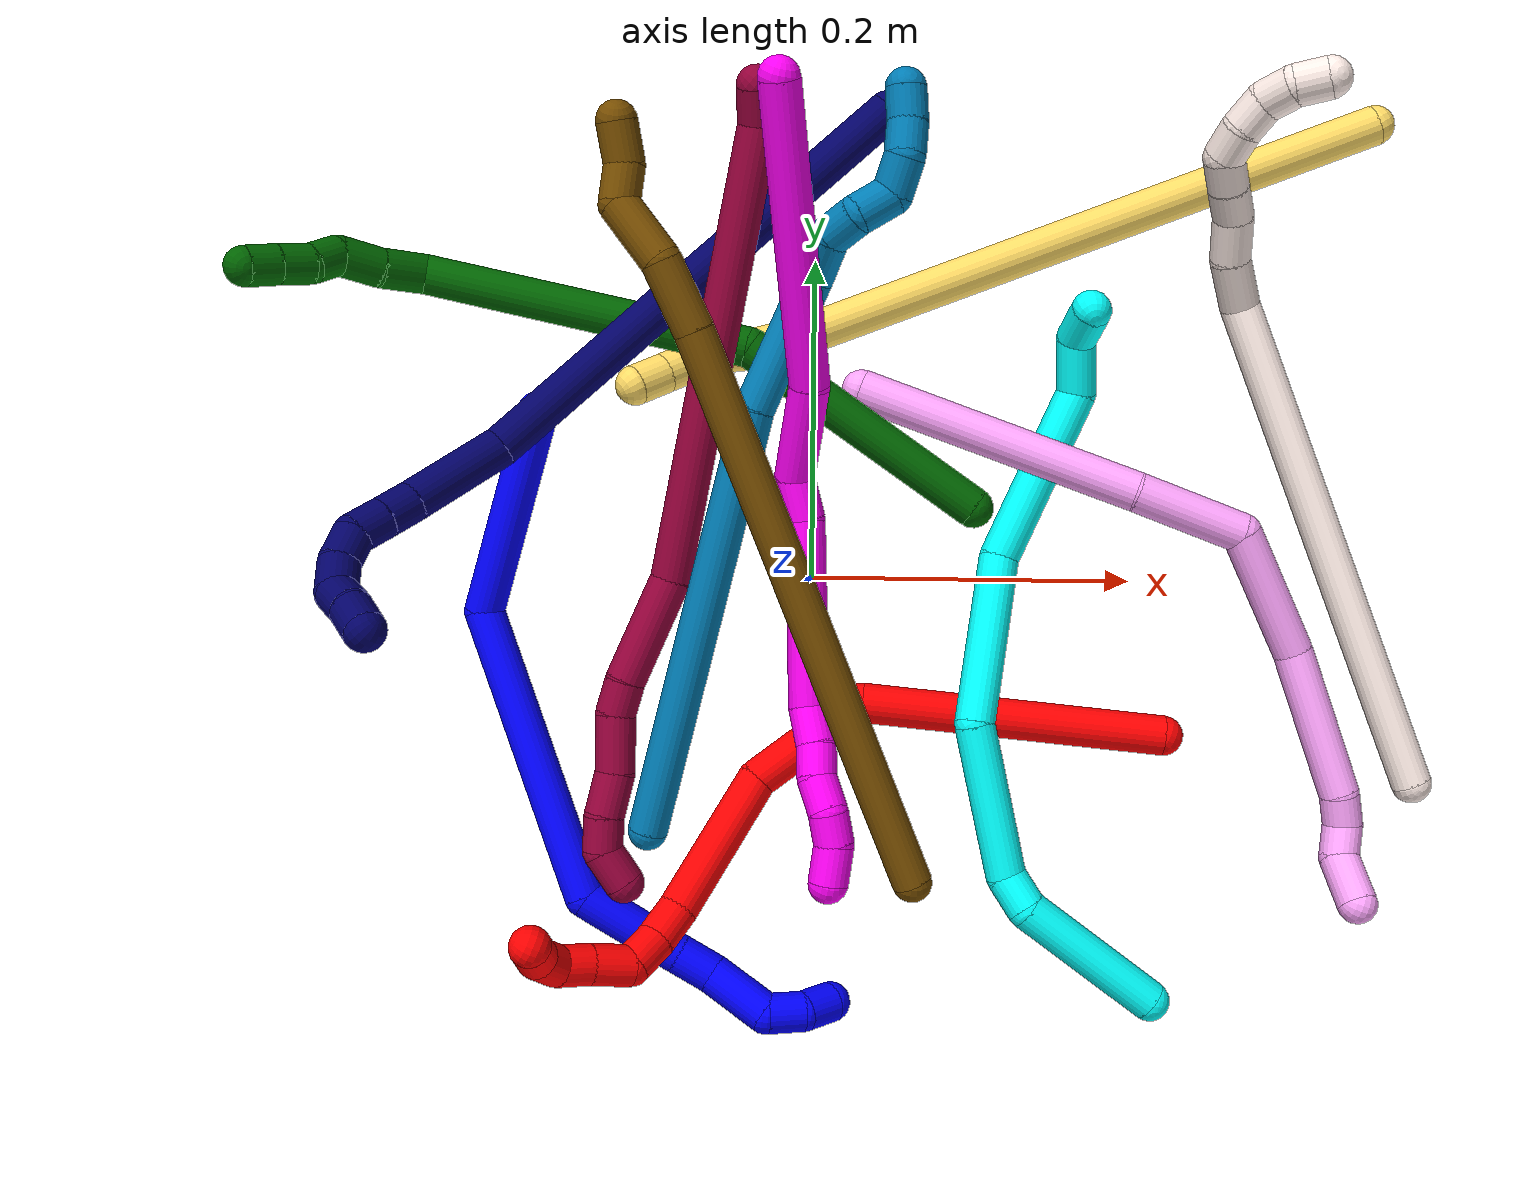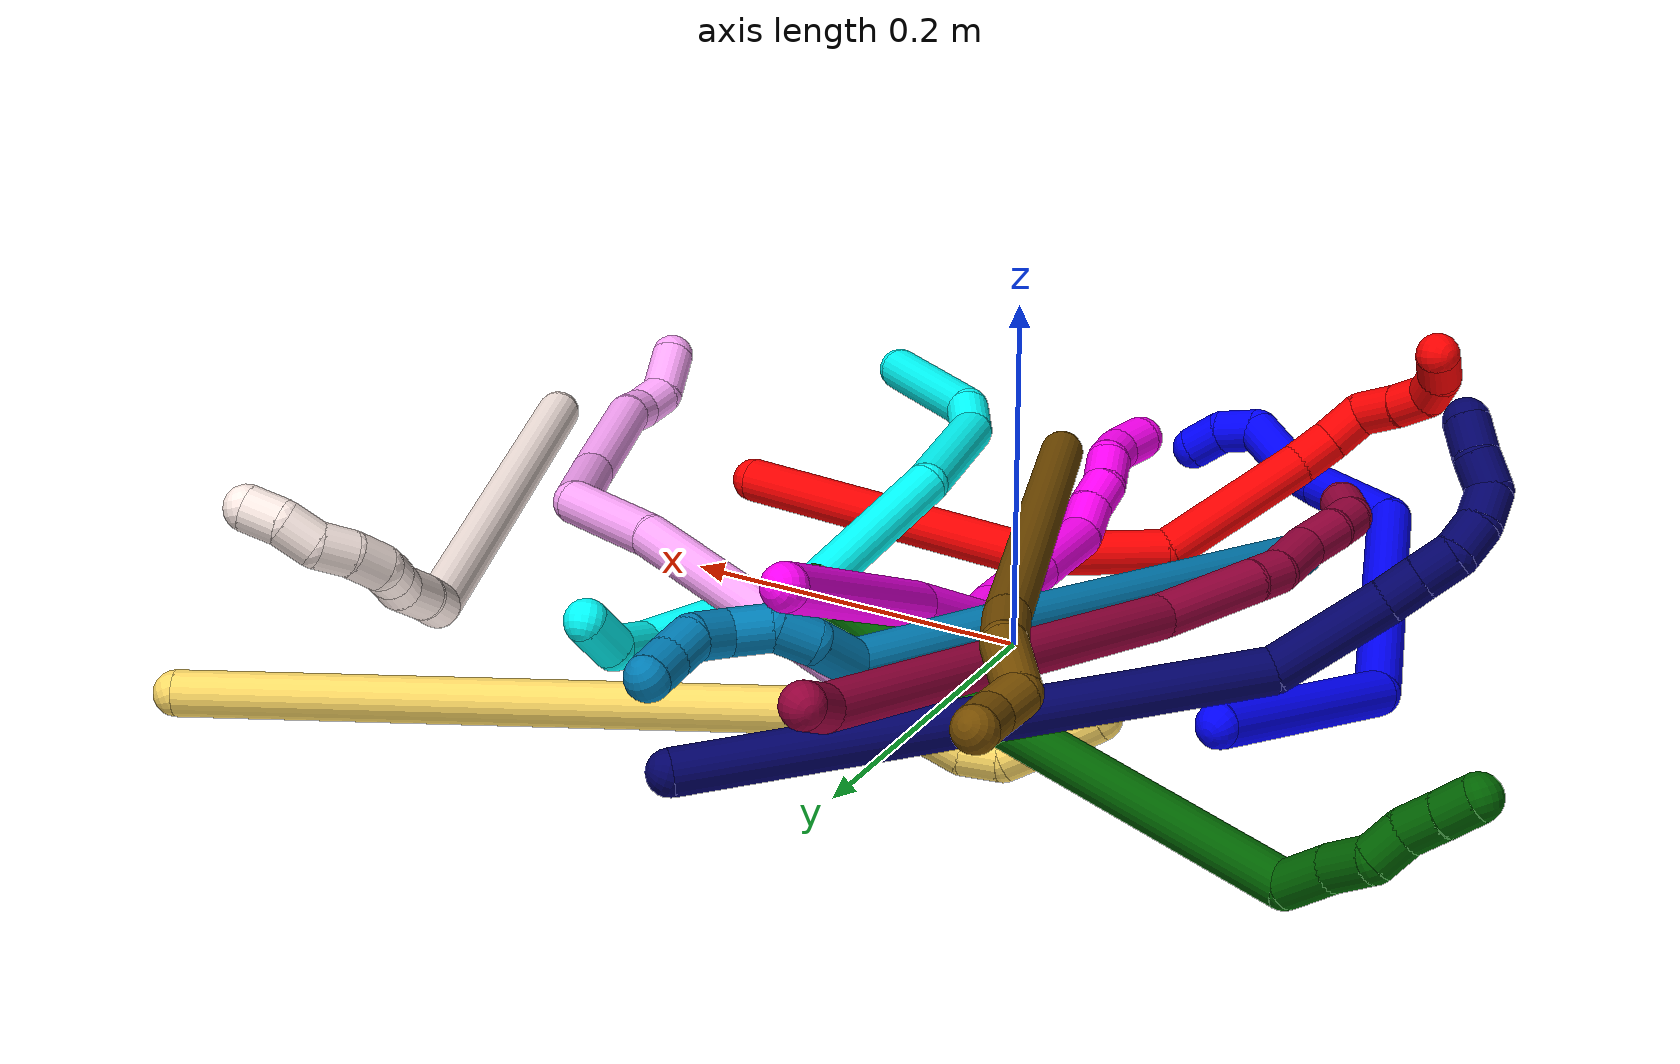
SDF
<sdf version="1.7">
 <world name="default">
  <plugin name="TubeGeneratorPlugin" filename="libtube_generator_plugin.so"/>
  <model name="photoneo_s_sensor">
   <static>1</static>
   <pose>0 0 2 1.57079 1.57079 3.14159</pose>
   <link name="link">
    <inertial><mass>0.1</mass></inertial>
    <sensor name="sensor" type="depth">
     <update_rate>30</update_rate>
     <camera>
      <horizontal_fov>1.22</horizontal_fov>
      <image><width>1920</width><height>1200</height><format>B8G8R8</format></image>
      <clip><near>0.1</near><far>4</far></clip>
      <depth_camera><output>points</output></depth_camera>
     </camera>
     <plugin name="camera_plugin" filename="libgazebo_ros_depth_camera.so">
      <baseline>0.2</baseline>
      <alwaysOn>1</alwaysOn>
      <updateRate>0.0</updateRate>
      <cameraName>camera_ir</cameraName>
      <imageTopicName>/camera/color/image_raw</imageTopicName>
      <cameraInfoTopicName>/camera/color/camera_info</cameraInfoTopicName>
      <depthImageTopicName>/camera/depth/image_raw</depthImageTopicName>
      <depthImageCameraInfoTopicName>/camera/depth/camera_info</depthImageCameraInfoTopicName>
      <pointCloudTopicName>/camera/depth/points</pointCloudTopicName>
      <frameName>fr_optical</frameName>
      <pointCloudCutoff>0.1</pointCloudCutoff>
      <pointCloudCutoffMax>2.0</pointCloudCutoffMax>
      <distortionK1>0</distortionK1>
      <distortionK2>0</distortionK2>
      <distortionK3>0</distortionK3>
      <distortionT1>0</distortionT1>
      <distortionT2>0</distortionT2>
      <CxPrime>0</CxPrime>
      <Cx>0</Cx>
      <Cy>0</Cy>
      <focalLength>0</focalLength>
      <hackBaseline>0</hackBaseline>
     </plugin>
    </sensor>
   </link>
  </model>
  <gravity>0 0 -9.8</gravity>
  <magnetic_field>6e-06 2.3e-05 -4.2e-05</magnetic_field>
  <atmosphere type="adiabatic"/>
  <physics name="default_physics" default="0" type="ode">
   <max_step_size>0.003</max_step_size>
   <real_time_factor>1</real_time_factor>
   <real_time_update_rate>1000</real_time_update_rate>
   <max_contacts>10000</max_contacts>
   <ode>
    <solver>
     <type>quick</type>
     <iters>100</iters>
     <sor>1.3</sor>
     <use_dynamic_moi_rescaling>0</use_dynamic_moi_rescaling>
    </solver>
    <constraints>
     <contact_max_correcting_vel>0</contact_max_correcting_vel>
     <contact_surface_layer>0.001</contact_surface_layer>
     <cfm>0</cfm>
     <erp>0.2</erp>
    </constraints>
   </ode>
  </physics>
  <scene><ambient>0.4 0.4 0.4 1</ambient><background>0.7 0.7 0.7 1</background><shadows>0</shadows></scene>
  <audio><device>default</device></audio>
  <spherical_coordinates>
   <surface_model>EARTH_WGS84</surface_model>
   <latitude_deg>0</latitude_deg>
   <longitude_deg>0</longitude_deg>
   <elevation>0</elevation>
   <heading_deg>0</heading_deg>
  </spherical_coordinates>
  <model name="bin">
   <static>1</static>
   <link name="bottom">
    <collision name="collision-bottom">
     <pose>0 0 -0.01 0 -0 0</pose>
     <geometry><box><size>0.8 0.6 0.02</size></box></geometry>
     <surface>
      <friction><ode><mu>100</mu><mu2>100</mu2></ode></friction>
      <contact><collide_bitmask>65535</collide_bitmask></contact>
     </surface>
    </collision>
   </link>
   <link name="west_wall">
    <collision name="collision-west_wall">
     <pose>-0.41 0 0.1 0 -0 0</pose>
     <geometry><box><size>0.02 0.6 0.2</size></box></geometry>
     <surface>
      <friction><ode><mu>100</mu><mu2>100</mu2></ode></friction>
      <contact><collide_bitmask>65535</collide_bitmask></contact>
     </surface>
    </collision>
   </link>
   <link name="east_wall">
    <collision name="collision-east_wall">
     <pose>0.41 0 0.1 0 -0 0</pose>
     <geometry><box><size>0.02 0.6 0.2</size></box></geometry>
     <surface>
      <friction><ode><mu>100</mu><mu2>100</mu2></ode></friction>
      <contact><collide_bitmask>65535</collide_bitmask></contact>
     </surface>
    </collision>
   </link>
   <link name="south_wall">
    <collision name="collision-south_wall">
     <pose>0 -0.31 0.1 0 -0 0</pose>
     <geometry><box><size>0.8 0.02 0.2</size></box></geometry>
     <surface>
      <friction><ode><mu>100</mu><mu2>100</mu2></ode></friction>
      <contact><collide_bitmask>65535</collide_bitmask></contact>
     </surface>
    </collision>
   </link>
   <link name="north_wall">
    <collision name="collision-north_wall">
     <pose>0 0.31 0.1 0 -0 0</pose>
     <geometry><box><size>0.8 0.02 0.2</size></box></geometry>
     <surface>
      <friction><ode><mu>100</mu><mu2>100</mu2></ode></friction>
      <contact><collide_bitmask>65535</collide_bitmask></contact>
     </surface>
    </collision>
   </link>
  </model>
  <model name="1">
   <static>0</static>
   <link name="1">
    <collision name="collision-cylinder-e_1_1_4">
     <pose>-0.021216 -0.006049 0.061939 0.097354 -0.328547 -0.016151</pose>
     <geometry><cylinder><radius>0.0125</radius><length>0.131501</length></cylinder></geometry>
     <surface>
      <friction><ode><mu>1.16</mu><mu2>1.16</mu2><slip1>0</slip1><slip2>0</slip2></ode></friction>
      <contact><ode><kp>1e+06</kp><kd>1</kd><max_vel>0</max_vel><min_depth>0.001</min_depth></ode></contact>
     </surface>
    </collision>
    <visual name="visual-cylinder-e_1_1_4">
     <pose>-0.021216 -0.006049 0.061939 0.097354 -0.328547 -0.016151</pose>
     <geometry><cylinder><radius>0.0125</radius><length>0.131501</length></cylinder></geometry>
     <material><ambient>0 0 1 1</ambient></material>
    </visual>
    <collision name="collision-cylinder-e_2_4_5">
     <pose>-0.011226 -0.042838 0.207549 0.352078 0.336739 0.060453</pose>
     <geometry><cylinder><radius>0.0125</radius><length>0.188887</length></cylinder></geometry>
     <surface>
      <friction><ode><mu>1.16</mu><mu2>1.16</mu2><slip1>0</slip1><slip2>0</slip2></ode></friction>
      <contact><ode><kp>1e+06</kp><kd>1</kd><max_vel>0</max_vel><min_depth>0.001</min_depth></ode></contact>
     </surface>
    </collision>
    <visual name="visual-cylinder-e_2_4_5">
     <pose>-0.011226 -0.042838 0.207549 0.352078 0.336739 0.060453</pose>
     <geometry><cylinder><radius>0.0125</radius><length>0.188887</length></cylinder></geometry>
     <material><ambient>0 0 1 1</ambient></material>
    </visual>
    <collision name="collision-cylinder-e_3_5_6">
     <pose>0.038149 -0.098653 0.305063 1.0664 0.565303 0.339534</pose>
     <geometry><cylinder><radius>0.0125</radius><length>0.06784</length></cylinder></geometry>
     <surface>
      <friction><ode><mu>1.16</mu><mu2>1.16</mu2><slip1>0</slip1><slip2>0</slip2></ode></friction>
      <contact><ode><kp>1e+06</kp><kd>1</kd><max_vel>0</max_vel><min_depth>0.001</min_depth></ode></contact>
     </surface>
    </collision>
    <visual name="visual-cylinder-e_3_5_6">
     <pose>0.038149 -0.098653 0.305063 1.0664 0.565303 0.339534</pose>
     <geometry><cylinder><radius>0.0125</radius><length>0.06784</length></cylinder></geometry>
     <material><ambient>0 0 1 1</ambient></material>
    </visual>
    <collision name="collision-cylinder-e_4_6_7">
     <pose>0.064275 -0.13233 0.323758 1.05712 0.678129 0.406244</pose>
     <geometry><cylinder><radius>0.0125</radius><length>0.025363</length></cylinder></geometry>
     <surface>
      <friction><ode><mu>1.16</mu><mu2>1.16</mu2><slip1>0</slip1><slip2>0</slip2></ode></friction>
      <contact><ode><kp>1e+06</kp><kd>1</kd><max_vel>0</max_vel><min_depth>0.001</min_depth></ode></contact>
     </surface>
    </collision>
    <visual name="visual-cylinder-e_4_6_7">
     <pose>0.064275 -0.13233 0.323758 1.05712 0.678129 0.406244</pose>
     <geometry><cylinder><radius>0.0125</radius><length>0.025363</length></cylinder></geometry>
     <material><ambient>0 0 1 1</ambient></material>
    </visual>
    <collision name="collision-cylinder-e_5_7_8">
     <pose>0.088254 -0.150532 0.337961 0.798612 0.874268 0.389369</pose>
     <geometry><cylinder><radius>0.0125</radius><length>0.041777</length></cylinder></geometry>
     <surface>
      <friction><ode><mu>1.16</mu><mu2>1.16</mu2><slip1>0</slip1><slip2>0</slip2></ode></friction>
      <contact><ode><kp>1e+06</kp><kd>1</kd><max_vel>0</max_vel><min_depth>0.001</min_depth></ode></contact>
     </surface>
    </collision>
    <visual name="visual-cylinder-e_5_7_8">
     <pose>0.088254 -0.150532 0.337961 0.798612 0.874268 0.389369</pose>
     <geometry><cylinder><radius>0.0125</radius><length>0.041777</length></cylinder></geometry>
     <material><ambient>0 0 1 1</ambient></material>
    </visual>
    <collision name="collision-cylinder-e_6_8_9">
     <pose>0.11025 -0.170014 0.345452 1.75676 0.536052 0.639516</pose>
     <geometry><cylinder><radius>0.0125</radius><length>0.02339</length></cylinder></geometry>
     <surface>
      <friction><ode><mu>1.16</mu><mu2>1.16</mu2><slip1>0</slip1><slip2>0</slip2></ode></friction>
      <contact><ode><kp>1e+06</kp><kd>1</kd><max_vel>0</max_vel><min_depth>0.001</min_depth></ode></contact>
     </surface>
    </collision>
    <visual name="visual-cylinder-e_6_8_9">
     <pose>0.11025 -0.170014 0.345452 1.75676 0.536052 0.639516</pose>
     <geometry><cylinder><radius>0.0125</radius><length>0.02339</length></cylinder></geometry>
     <material><ambient>0 0 1 1</ambient></material>
    </visual>
    <collision name="collision-cylinder-e_7_9_2">
     <pose>0.117585 -0.189938 0.340416 1.87718 0.128528 0.175257</pose>
     <geometry><cylinder><radius>0.0125</radius><length>0.021242</length></cylinder></geometry>
     <surface>
      <friction><ode><mu>1.16</mu><mu2>1.16</mu2><slip1>0</slip1><slip2>0</slip2></ode></friction>
      <contact><ode><kp>1e+06</kp><kd>1</kd><max_vel>0</max_vel><min_depth>0.001</min_depth></ode></contact>
     </surface>
    </collision>
    <visual name="visual-cylinder-e_7_9_2">
     <pose>0.117585 -0.189938 0.340416 1.87718 0.128528 0.175257</pose>
     <geometry><cylinder><radius>0.0125</radius><length>0.021242</length></cylinder></geometry>
     <material><ambient>0 0 1 1</ambient></material>
    </visual>
    <collision name="collision-sphere-2">
     <pose>0.118946 -0.199981 0.337239 0 -0 0</pose>
     <geometry><sphere><radius>0.0125</radius></sphere></geometry>
     <surface>
      <friction><ode><mu>1.16</mu><mu2>1.16</mu2><slip1>0</slip1><slip2>0</slip2></ode></friction>
      <contact><ode><kp>1e+06</kp><kd>1</kd><max_vel>0</max_vel><min_depth>0.001</min_depth></ode></contact>
     </surface>
    </collision>
    <visual name="visual-sphere-2">
     <pose>0.118946 -0.199981 0.337239 0 -0 0</pose>
     <geometry><sphere><radius>0.0125</radius></sphere></geometry>
     <material><ambient>0 0 1 1</ambient></material>
    </visual>
    <collision name="collision-sphere-9">
     <pose>0.116223 -0.179895 0.343593 0 -0 0</pose>
     <geometry><sphere><radius>0.0125</radius></sphere></geometry>
     <surface>
      <friction><ode><mu>1.16</mu><mu2>1.16</mu2><slip1>0</slip1><slip2>0</slip2></ode></friction>
      <contact><ode><kp>1e+06</kp><kd>1</kd><max_vel>0</max_vel><min_depth>0.001</min_depth></ode></contact>
     </surface>
    </collision>
    <visual name="visual-sphere-9">
     <pose>0.116223 -0.179895 0.343593 0 -0 0</pose>
     <geometry><sphere><radius>0.0125</radius></sphere></geometry>
     <material><ambient>0 0 1 1</ambient></material>
    </visual>
    <collision name="collision-sphere-4">
     <pose>-0.042431 -0.012098 0.123878 0 -0 0</pose>
     <geometry><sphere><radius>0.0125</radius></sphere></geometry>
     <surface>
      <friction><ode><mu>1.16</mu><mu2>1.16</mu2><slip1>0</slip1><slip2>0</slip2></ode></friction>
      <contact><ode><kp>1e+06</kp><kd>1</kd><max_vel>0</max_vel><min_depth>0.001</min_depth></ode></contact>
     </surface>
    </collision>
    <visual name="visual-sphere-4">
     <pose>-0.042431 -0.012098 0.123878 0 -0 0</pose>
     <geometry><sphere><radius>0.0125</radius></sphere></geometry>
     <material><ambient>0 0 1 1</ambient></material>
    </visual>
    <collision name="collision-sphere-1">
     <geometry><sphere><radius>0.0125</radius></sphere></geometry>
     <surface>
      <friction><ode><mu>1.16</mu><mu2>1.16</mu2><slip1>0</slip1><slip2>0</slip2></ode></friction>
      <contact><ode><kp>1e+06</kp><kd>1</kd><max_vel>0</max_vel><min_depth>0.001</min_depth></ode></contact>
     </surface>
    </collision>
    <visual name="visual-sphere-1">
     <geometry><sphere><radius>0.0125</radius></sphere></geometry>
     <material><ambient>0 0 1 1</ambient></material>
    </visual>
    <collision name="collision-sphere-8">
     <pose>0.104277 -0.160133 0.347311 0 -0 0</pose>
     <geometry><sphere><radius>0.0125</radius></sphere></geometry>
     <surface>
      <friction><ode><mu>1.16</mu><mu2>1.16</mu2><slip1>0</slip1><slip2>0</slip2></ode></friction>
      <contact><ode><kp>1e+06</kp><kd>1</kd><max_vel>0</max_vel><min_depth>0.001</min_depth></ode></contact>
     </surface>
    </collision>
    <visual name="visual-sphere-8">
     <pose>0.104277 -0.160133 0.347311 0 -0 0</pose>
     <geometry><sphere><radius>0.0125</radius></sphere></geometry>
     <material><ambient>0 0 1 1</ambient></material>
    </visual>
    <collision name="collision-sphere-5">
     <pose>0.019979 -0.073577 0.29122 0 -0 0</pose>
     <geometry><sphere><radius>0.0125</radius></sphere></geometry>
     <surface>
      <friction><ode><mu>1.16</mu><mu2>1.16</mu2><slip1>0</slip1><slip2>0</slip2></ode></friction>
      <contact><ode><kp>1e+06</kp><kd>1</kd><max_vel>0</max_vel><min_depth>0.001</min_depth></ode></contact>
     </surface>
    </collision>
    <visual name="visual-sphere-5">
     <pose>0.019979 -0.073577 0.29122 0 -0 0</pose>
     <geometry><sphere><radius>0.0125</radius></sphere></geometry>
     <material><ambient>0 0 1 1</ambient></material>
    </visual>
    <collision name="collision-sphere-6">
     <pose>0.056319 -0.123729 0.318905 0 -0 0</pose>
     <geometry><sphere><radius>0.0125</radius></sphere></geometry>
     <surface>
      <friction><ode><mu>1.16</mu><mu2>1.16</mu2><slip1>0</slip1><slip2>0</slip2></ode></friction>
      <contact><ode><kp>1e+06</kp><kd>1</kd><max_vel>0</max_vel><min_depth>0.001</min_depth></ode></contact>
     </surface>
    </collision>
    <visual name="visual-sphere-6">
     <pose>0.056319 -0.123729 0.318905 0 -0 0</pose>
     <geometry><sphere><radius>0.0125</radius></sphere></geometry>
     <material><ambient>0 0 1 1</ambient></material>
    </visual>
    <collision name="collision-sphere-7">
     <pose>0.07223 -0.140932 0.328611 0 -0 0</pose>
     <geometry><sphere><radius>0.0125</radius></sphere></geometry>
     <surface>
      <friction><ode><mu>1.16</mu><mu2>1.16</mu2><slip1>0</slip1><slip2>0</slip2></ode></friction>
      <contact><ode><kp>1e+06</kp><kd>1</kd><max_vel>0</max_vel><min_depth>0.001</min_depth></ode></contact>
     </surface>
    </collision>
    <visual name="visual-sphere-7">
     <pose>0.07223 -0.140932 0.328611 0 -0 0</pose>
     <geometry><sphere><radius>0.0125</radius></sphere></geometry>
     <material><ambient>0 0 1 1</ambient></material>
    </visual>
    <inertial>
     <pose>0.016143 -0.066472 0.211371 0 -0 0</pose>
     <mass>0.5</mass>
     <inertia>
      <ixx>0.000803</ixx>
      <ixy>0</ixy>
      <ixz>0</ixz>
      <iyy>0.000782</iyy>
      <iyz>0</iyz>
      <izz>0.00011</izz>
     </inertia>
    </inertial>
   </link>
   <pose>-0.167937 0.099958 0.039717 1.45302 -0.785801 -0.036709</pose>
  </model>
  <model name="2">
   <static>0</static>
   <link name="2">
    <collision name="collision-cylinder-e_1_1_4">
     <pose>-0.018716 -0.030918 -0.087766 2.80289 -0.198487 -1.05465</pose>
     <geometry><cylinder><radius>0.0125</radius><length>0.189833</length></cylinder></geometry>
     <surface>
      <friction><ode><mu>1.16</mu><mu2>1.16</mu2><slip1>0</slip1><slip2>0</slip2></ode></friction>
      <contact><ode><kp>1e+06</kp><kd>1</kd><max_vel>0</max_vel><min_depth>0.001</min_depth></ode></contact>
     </surface>
    </collision>
    <visual name="visual-cylinder-e_1_1_4">
     <pose>-0.018716 -0.030918 -0.087766 2.80289 -0.198487 -1.05465</pose>
     <geometry><cylinder><radius>0.0125</radius><length>0.189833</length></cylinder></geometry>
     <material><ambient>1 0 0 1</ambient></material>
    </visual>
    <collision name="collision-cylinder-e_2_4_5">
     <pose>-0.066032 -0.083918 -0.193856 2.26344 -0.783738 -1.44318</pose>
     <geometry><cylinder><radius>0.0125</radius><length>0.081025</length></cylinder></geometry>
     <surface>
      <friction><ode><mu>1.16</mu><mu2>1.16</mu2><slip1>0</slip1><slip2>0</slip2></ode></friction>
      <contact><ode><kp>1e+06</kp><kd>1</kd><max_vel>0</max_vel><min_depth>0.001</min_depth></ode></contact>
     </surface>
    </collision>
    <visual name="visual-cylinder-e_2_4_5">
     <pose>-0.066032 -0.083918 -0.193856 2.26344 -0.783738 -1.44318</pose>
     <geometry><cylinder><radius>0.0125</radius><length>0.081025</length></cylinder></geometry>
     <material><ambient>1 0 0 1</ambient></material>
    </visual>
    <collision name="collision-cylinder-e_3_5_6">
     <pose>-0.141027 -0.113346 -0.220769 2.43406 -1.33183 -2.26275</pose>
     <geometry><cylinder><radius>0.0125</radius><length>0.095508</length></cylinder></geometry>
     <surface>
      <friction><ode><mu>1.16</mu><mu2>1.16</mu2><slip1>0</slip1><slip2>0</slip2></ode></friction>
      <contact><ode><kp>1e+06</kp><kd>1</kd><max_vel>0</max_vel><min_depth>0.001</min_depth></ode></contact>
     </surface>
    </collision>
    <visual name="visual-cylinder-e_3_5_6">
     <pose>-0.141027 -0.113346 -0.220769 2.43406 -1.33183 -2.26275</pose>
     <geometry><cylinder><radius>0.0125</radius><length>0.095508</length></cylinder></geometry>
     <material><ambient>1 0 0 1</ambient></material>
    </visual>
    <collision name="collision-cylinder-e_4_6_7">
     <pose>-0.19873 -0.121118 -0.232638 3.01266 -1.2863 -2.96974</pose>
     <geometry><cylinder><radius>0.0125</radius><length>0.023558</length></cylinder></geometry>
     <surface>
      <friction><ode><mu>1.16</mu><mu2>1.16</mu2><slip1>0</slip1><slip2>0</slip2></ode></friction>
      <contact><ode><kp>1e+06</kp><kd>1</kd><max_vel>0</max_vel><min_depth>0.001</min_depth></ode></contact>
     </surface>
    </collision>
    <visual name="visual-cylinder-e_4_6_7">
     <pose>-0.19873 -0.121118 -0.232638 3.01266 -1.2863 -2.96974</pose>
     <geometry><cylinder><radius>0.0125</radius><length>0.023558</length></cylinder></geometry>
     <material><ambient>1 0 0 1</ambient></material>
    </visual>
    <collision name="collision-cylinder-e_5_7_8">
     <pose>-0.220653 -0.120003 -0.240739 -2.83239 -1.1259 2.65738</pose>
     <geometry><cylinder><radius>0.0125</radius><length>0.023526</length></cylinder></geometry>
     <surface>
      <friction><ode><mu>1.16</mu><mu2>1.16</mu2><slip1>0</slip1><slip2>0</slip2></ode></friction>
      <contact><ode><kp>1e+06</kp><kd>1</kd><max_vel>0</max_vel><min_depth>0.001</min_depth></ode></contact>
     </surface>
    </collision>
    <visual name="visual-cylinder-e_5_7_8">
     <pose>-0.220653 -0.120003 -0.240739 -2.83239 -1.1259 2.65738</pose>
     <geometry><cylinder><radius>0.0125</radius><length>0.023526</length></cylinder></geometry>
     <material><ambient>1 0 0 1</ambient></material>
    </visual>
    <collision name="collision-cylinder-e_6_8_9">
     <pose>-0.235789 -0.117644 -0.257601 -3.07372 -0.358248 2.77092</pose>
     <geometry><cylinder><radius>0.0125</radius><length>0.025772</length></cylinder></geometry>
     <surface>
      <friction><ode><mu>1.16</mu><mu2>1.16</mu2><slip1>0</slip1><slip2>0</slip2></ode></friction>
      <contact><ode><kp>1e+06</kp><kd>1</kd><max_vel>0</max_vel><min_depth>0.001</min_depth></ode></contact>
     </surface>
    </collision>
    <visual name="visual-cylinder-e_6_8_9">
     <pose>-0.235789 -0.117644 -0.257601 -3.07372 -0.358248 2.77092</pose>
     <geometry><cylinder><radius>0.0125</radius><length>0.025772</length></cylinder></geometry>
     <material><ambient>1 0 0 1</ambient></material>
    </visual>
    <collision name="collision-cylinder-e_7_9_10">
     <pose>-0.244834 -0.115692 -0.278798 -3.01843 -0.456097 2.62225</pose>
     <geometry><cylinder><radius>0.0125</radius><length>0.020554</length></cylinder></geometry>
     <surface>
      <friction><ode><mu>1.16</mu><mu2>1.16</mu2><slip1>0</slip1><slip2>0</slip2></ode></friction>
      <contact><ode><kp>1e+06</kp><kd>1</kd><max_vel>0</max_vel><min_depth>0.001</min_depth></ode></contact>
     </surface>
    </collision>
    <visual name="visual-cylinder-e_7_9_10">
     <pose>-0.244834 -0.115692 -0.278798 -3.01843 -0.456097 2.62225</pose>
     <geometry><cylinder><radius>0.0125</radius><length>0.020554</length></cylinder></geometry>
     <material><ambient>1 0 0 1</ambient></material>
    </visual>
    <collision name="collision-cylinder-e_8_10_11">
     <pose>-0.251087 -0.108024 -0.295393 -2.42087 -0.172629 0.451441</pose>
     <geometry><cylinder><radius>0.0125</radius><length>0.020101</length></cylinder></geometry>
     <surface>
      <friction><ode><mu>1.16</mu><mu2>1.16</mu2><slip1>0</slip1><slip2>0</slip2></ode></friction>
      <contact><ode><kp>1e+06</kp><kd>1</kd><max_vel>0</max_vel><min_depth>0.001</min_depth></ode></contact>
     </surface>
    </collision>
    <visual name="visual-cylinder-e_8_10_11">
     <pose>-0.251087 -0.108024 -0.295393 -2.42087 -0.172629 0.451441</pose>
     <geometry><cylinder><radius>0.0125</radius><length>0.020101</length></cylinder></geometry>
     <material><ambient>1 0 0 1</ambient></material>
    </visual>
    <collision name="collision-cylinder-e_9_11_2">
     <pose>-0.252908 -0.092569 -0.307485 -2.05153 -0.009446 0.01558</pose>
     <geometry><cylinder><radius>0.0125</radius><length>0.020124</length></cylinder></geometry>
     <surface>
      <friction><ode><mu>1.16</mu><mu2>1.16</mu2><slip1>0</slip1><slip2>0</slip2></ode></friction>
      <contact><ode><kp>1e+06</kp><kd>1</kd><max_vel>0</max_vel><min_depth>0.001</min_depth></ode></contact>
     </surface>
    </collision>
    <visual name="visual-cylinder-e_9_11_2">
     <pose>-0.252908 -0.092569 -0.307485 -2.05153 -0.009446 0.01558</pose>
     <geometry><cylinder><radius>0.0125</radius><length>0.020124</length></cylinder></geometry>
     <material><ambient>1 0 0 1</ambient></material>
    </visual>
    <collision name="collision-sphere-2">
     <pose>-0.253003 -0.083648 -0.312138 0 -0 0</pose>
     <geometry><sphere><radius>0.0125</radius></sphere></geometry>
     <surface>
      <friction><ode><mu>1.16</mu><mu2>1.16</mu2><slip1>0</slip1><slip2>0</slip2></ode></friction>
      <contact><ode><kp>1e+06</kp><kd>1</kd><max_vel>0</max_vel><min_depth>0.001</min_depth></ode></contact>
     </surface>
    </collision>
    <visual name="visual-sphere-2">
     <pose>-0.253003 -0.083648 -0.312138 0 -0 0</pose>
     <geometry><sphere><radius>0.0125</radius></sphere></geometry>
     <material><ambient>1 0 0 1</ambient></material>
    </visual>
    <collision name="collision-sphere-11">
     <pose>-0.252813 -0.10149 -0.302832 0 -0 0</pose>
     <geometry><sphere><radius>0.0125</radius></sphere></geometry>
     <surface>
      <friction><ode><mu>1.16</mu><mu2>1.16</mu2><slip1>0</slip1><slip2>0</slip2></ode></friction>
      <contact><ode><kp>1e+06</kp><kd>1</kd><max_vel>0</max_vel><min_depth>0.001</min_depth></ode></contact>
     </surface>
    </collision>
    <visual name="visual-sphere-11">
     <pose>-0.252813 -0.10149 -0.302832 0 -0 0</pose>
     <geometry><sphere><radius>0.0125</radius></sphere></geometry>
     <material><ambient>1 0 0 1</ambient></material>
    </visual>
    <collision name="collision-sphere-10">
     <pose>-0.24936 -0.114558 -0.287954 0 -0 0</pose>
     <geometry><sphere><radius>0.0125</radius></sphere></geometry>
     <surface>
      <friction><ode><mu>1.16</mu><mu2>1.16</mu2><slip1>0</slip1><slip2>0</slip2></ode></friction>
      <contact><ode><kp>1e+06</kp><kd>1</kd><max_vel>0</max_vel><min_depth>0.001</min_depth></ode></contact>
     </surface>
    </collision>
    <visual name="visual-sphere-10">
     <pose>-0.24936 -0.114558 -0.287954 0 -0 0</pose>
     <geometry><sphere><radius>0.0125</radius></sphere></geometry>
     <material><ambient>1 0 0 1</ambient></material>
    </visual>
    <collision name="collision-sphere-9">
     <pose>-0.240307 -0.116825 -0.269641 0 -0 0</pose>
     <geometry><sphere><radius>0.0125</radius></sphere></geometry>
     <surface>
      <friction><ode><mu>1.16</mu><mu2>1.16</mu2><slip1>0</slip1><slip2>0</slip2></ode></friction>
      <contact><ode><kp>1e+06</kp><kd>1</kd><max_vel>0</max_vel><min_depth>0.001</min_depth></ode></contact>
     </surface>
    </collision>
    <visual name="visual-sphere-9">
     <pose>-0.240307 -0.116825 -0.269641 0 -0 0</pose>
     <geometry><sphere><radius>0.0125</radius></sphere></geometry>
     <material><ambient>1 0 0 1</ambient></material>
    </visual>
    <collision name="collision-sphere-4">
     <pose>-0.037432 -0.061836 -0.175533 0 -0 0</pose>
     <geometry><sphere><radius>0.0125</radius></sphere></geometry>
     <surface>
      <friction><ode><mu>1.16</mu><mu2>1.16</mu2><slip1>0</slip1><slip2>0</slip2></ode></friction>
      <contact><ode><kp>1e+06</kp><kd>1</kd><max_vel>0</max_vel><min_depth>0.001</min_depth></ode></contact>
     </surface>
    </collision>
    <visual name="visual-sphere-4">
     <pose>-0.037432 -0.061836 -0.175533 0 -0 0</pose>
     <geometry><sphere><radius>0.0125</radius></sphere></geometry>
     <material><ambient>1 0 0 1</ambient></material>
    </visual>
    <collision name="collision-sphere-1">
     <geometry><sphere><radius>0.0125</radius></sphere></geometry>
     <surface>
      <friction><ode><mu>1.16</mu><mu2>1.16</mu2><slip1>0</slip1><slip2>0</slip2></ode></friction>
      <contact><ode><kp>1e+06</kp><kd>1</kd><max_vel>0</max_vel><min_depth>0.001</min_depth></ode></contact>
     </surface>
    </collision>
    <visual name="visual-sphere-1">
     <geometry><sphere><radius>0.0125</radius></sphere></geometry>
     <material><ambient>1 0 0 1</ambient></material>
    </visual>
    <collision name="collision-sphere-8">
     <pose>-0.231271 -0.118462 -0.245561 0 -0 0</pose>
     <geometry><sphere><radius>0.0125</radius></sphere></geometry>
     <surface>
      <friction><ode><mu>1.16</mu><mu2>1.16</mu2><slip1>0</slip1><slip2>0</slip2></ode></friction>
      <contact><ode><kp>1e+06</kp><kd>1</kd><max_vel>0</max_vel><min_depth>0.001</min_depth></ode></contact>
     </surface>
    </collision>
    <visual name="visual-sphere-8">
     <pose>-0.231271 -0.118462 -0.245561 0 -0 0</pose>
     <geometry><sphere><radius>0.0125</radius></sphere></geometry>
     <material><ambient>1 0 0 1</ambient></material>
    </visual>
    <collision name="collision-sphere-5">
     <pose>-0.094631 -0.106 -0.212179 0 -0 0</pose>
     <geometry><sphere><radius>0.0125</radius></sphere></geometry>
     <surface>
      <friction><ode><mu>1.16</mu><mu2>1.16</mu2><slip1>0</slip1><slip2>0</slip2></ode></friction>
      <contact><ode><kp>1e+06</kp><kd>1</kd><max_vel>0</max_vel><min_depth>0.001</min_depth></ode></contact>
     </surface>
    </collision>
    <visual name="visual-sphere-5">
     <pose>-0.094631 -0.106 -0.212179 0 -0 0</pose>
     <geometry><sphere><radius>0.0125</radius></sphere></geometry>
     <material><ambient>1 0 0 1</ambient></material>
    </visual>
    <collision name="collision-sphere-6">
     <pose>-0.187424 -0.120693 -0.22936 0 -0 0</pose>
     <geometry><sphere><radius>0.0125</radius></sphere></geometry>
     <surface>
      <friction><ode><mu>1.16</mu><mu2>1.16</mu2><slip1>0</slip1><slip2>0</slip2></ode></friction>
      <contact><ode><kp>1e+06</kp><kd>1</kd><max_vel>0</max_vel><min_depth>0.001</min_depth></ode></contact>
     </surface>
    </collision>
    <visual name="visual-sphere-6">
     <pose>-0.187424 -0.120693 -0.22936 0 -0 0</pose>
     <geometry><sphere><radius>0.0125</radius></sphere></geometry>
     <material><ambient>1 0 0 1</ambient></material>
    </visual>
    <collision name="collision-sphere-7">
     <pose>-0.210035 -0.121543 -0.235917 0 -0 0</pose>
     <geometry><sphere><radius>0.0125</radius></sphere></geometry>
     <surface>
      <friction><ode><mu>1.16</mu><mu2>1.16</mu2><slip1>0</slip1><slip2>0</slip2></ode></friction>
      <contact><ode><kp>1e+06</kp><kd>1</kd><max_vel>0</max_vel><min_depth>0.001</min_depth></ode></contact>
     </surface>
    </collision>
    <visual name="visual-sphere-7">
     <pose>-0.210035 -0.121543 -0.235917 0 -0 0</pose>
     <geometry><sphere><radius>0.0125</radius></sphere></geometry>
     <material><ambient>1 0 0 1</ambient></material>
    </visual>
    <inertial>
     <pose>-0.106981 -0.077229 -0.178184 0 -0 0</pose>
     <mass>0.5</mass>
     <inertia>
      <ixx>-0.000287</ixx>
      <ixy>0</ixy>
      <ixz>0</ixz>
      <iyy>-0.000678</iyy>
      <iyz>0</iyz>
      <izz>0.000426</izz>
     </inertia>
    </inertial>
   </link>
   <pose>0.221542 -0.096057 0.011497 1.82387 0.481868 1.25806</pose>
  </model>
  <model name="3">
   <static>0</static>
   <link name="3">
    <collision name="collision-cylinder-e_1_1_4">
     <pose>-0.016911 0.040399 -0.021693 -2.06359 -0.353323 0.580153</pose>
     <geometry><cylinder><radius>0.0125</radius><length>0.097748</length></cylinder></geometry>
     <surface>
      <friction><ode><mu>1.16</mu><mu2>1.16</mu2><slip1>0</slip1><slip2>0</slip2></ode></friction>
      <contact><ode><kp>1e+06</kp><kd>1</kd><max_vel>0</max_vel><min_depth>0.001</min_depth></ode></contact>
     </surface>
    </collision>
    <visual name="visual-cylinder-e_1_1_4">
     <pose>-0.016911 0.040399 -0.021693 -2.06359 -0.353323 0.580153</pose>
     <geometry><cylinder><radius>0.0125</radius><length>0.097748</length></cylinder></geometry>
     <material><ambient>0.003922 1 0.996078 1</ambient></material>
    </visual>
    <collision name="collision-cylinder-e_2_4_5">
     <pose>-0.035006 0.087976 -0.052627 -2.48109 -0.100782 0.292145</pose>
     <geometry><cylinder><radius>0.0125</radius><length>0.023522</length></cylinder></geometry>
     <surface>
      <friction><ode><mu>1.16</mu><mu2>1.16</mu2><slip1>0</slip1><slip2>0</slip2></ode></friction>
      <contact><ode><kp>1e+06</kp><kd>1</kd><max_vel>0</max_vel><min_depth>0.001</min_depth></ode></contact>
     </surface>
    </collision>
    <visual name="visual-cylinder-e_2_4_5">
     <pose>-0.035006 0.087976 -0.052627 -2.48109 -0.100782 0.292145</pose>
     <geometry><cylinder><radius>0.0125</radius><length>0.023522</length></cylinder></geometry>
     <material><ambient>0.003922 1 0.996078 1</ambient></material>
    </visual>
    <collision name="collision-cylinder-e_3_5_6">
     <pose>-0.021079 0.129676 -0.092235 -2.29228 0.317527 -0.680635</pose>
     <geometry><cylinder><radius>0.0125</radius><length>0.096792</length></cylinder></geometry>
     <surface>
      <friction><ode><mu>1.16</mu><mu2>1.16</mu2><slip1>0</slip1><slip2>0</slip2></ode></friction>
      <contact><ode><kp>1e+06</kp><kd>1</kd><max_vel>0</max_vel><min_depth>0.001</min_depth></ode></contact>
     </surface>
    </collision>
    <visual name="visual-cylinder-e_3_5_6">
     <pose>-0.021079 0.129676 -0.092235 -2.29228 0.317527 -0.680635</pose>
     <geometry><cylinder><radius>0.0125</radius><length>0.096792</length></cylinder></geometry>
     <material><ambient>0.003922 1 0.996078 1</ambient></material>
    </visual>
    <collision name="collision-cylinder-e_4_6_7">
     <pose>0.022253 0.180715 -0.164682 -2.76753 0.558095 -1.97418</pose>
     <geometry><cylinder><radius>0.0125</radius><length>0.106583</length></cylinder></geometry>
     <surface>
      <friction><ode><mu>1.16</mu><mu2>1.16</mu2><slip1>0</slip1><slip2>0</slip2></ode></friction>
      <contact><ode><kp>1e+06</kp><kd>1</kd><max_vel>0</max_vel><min_depth>0.001</min_depth></ode></contact>
     </surface>
    </collision>
    <visual name="visual-cylinder-e_4_6_7">
     <pose>0.022253 0.180715 -0.164682 -2.76753 0.558095 -1.97418</pose>
     <geometry><cylinder><radius>0.0125</radius><length>0.106583</length></cylinder></geometry>
     <material><ambient>0.003922 1 0.996078 1</ambient></material>
    </visual>
    <collision name="collision-cylinder-e_5_7_8">
     <pose>0.095133 0.213399 -0.237935 -2.66318 0.904446 -2.21108</pose>
     <geometry><cylinder><radius>0.0125</radius><length>0.113623</length></cylinder></geometry>
     <surface>
      <friction><ode><mu>1.16</mu><mu2>1.16</mu2><slip1>0</slip1><slip2>0</slip2></ode></friction>
      <contact><ode><kp>1e+06</kp><kd>1</kd><max_vel>0</max_vel><min_depth>0.001</min_depth></ode></contact>
     </surface>
    </collision>
    <visual name="visual-cylinder-e_5_7_8">
     <pose>0.095133 0.213399 -0.237935 -2.66318 0.904446 -2.21108</pose>
     <geometry><cylinder><radius>0.0125</radius><length>0.113623</length></cylinder></geometry>
     <material><ambient>0.003922 1 0.996078 1</ambient></material>
    </visual>
    <collision name="collision-cylinder-e_6_8_9">
     <pose>0.148523 0.243193 -0.275849 -2.03015 0.521356 -0.811425</pose>
     <geometry><cylinder><radius>0.0125</radius><length>0.035064</length></cylinder></geometry>
     <surface>
      <friction><ode><mu>1.16</mu><mu2>1.16</mu2><slip1>0</slip1><slip2>0</slip2></ode></friction>
      <contact><ode><kp>1e+06</kp><kd>1</kd><max_vel>0</max_vel><min_depth>0.001</min_depth></ode></contact>
     </surface>
    </collision>
    <visual name="visual-cylinder-e_6_8_9">
     <pose>0.148523 0.243193 -0.275849 -2.03015 0.521356 -0.811425</pose>
     <geometry><cylinder><radius>0.0125</radius><length>0.035064</length></cylinder></geometry>
     <material><ambient>0.003922 1 0.996078 1</ambient></material>
    </visual>
    <collision name="collision-cylinder-e_7_9_2">
     <pose>0.166404 0.266021 -0.27952 -1.24879 0.756167 -0.557502</pose>
     <geometry><cylinder><radius>0.0125</radius><length>0.026668</length></cylinder></geometry>
     <surface>
      <friction><ode><mu>1.16</mu><mu2>1.16</mu2><slip1>0</slip1><slip2>0</slip2></ode></friction>
      <contact><ode><kp>1e+06</kp><kd>1</kd><max_vel>0</max_vel><min_depth>0.001</min_depth></ode></contact>
     </surface>
    </collision>
    <visual name="visual-cylinder-e_7_9_2">
     <pose>0.166404 0.266021 -0.27952 -1.24879 0.756167 -0.557502</pose>
     <geometry><cylinder><radius>0.0125</radius><length>0.026668</length></cylinder></geometry>
     <material><ambient>0.003922 1 0.996078 1</ambient></material>
    </visual>
    <collision name="collision-sphere-2">
     <pose>0.175554 0.275223 -0.27645 0 -0 0</pose>
     <geometry><sphere><radius>0.0125</radius></sphere></geometry>
     <surface>
      <friction><ode><mu>1.16</mu><mu2>1.16</mu2><slip1>0</slip1><slip2>0</slip2></ode></friction>
      <contact><ode><kp>1e+06</kp><kd>1</kd><max_vel>0</max_vel><min_depth>0.001</min_depth></ode></contact>
     </surface>
    </collision>
    <visual name="visual-sphere-2">
     <pose>0.175554 0.275223 -0.27645 0 -0 0</pose>
     <geometry><sphere><radius>0.0125</radius></sphere></geometry>
     <material><ambient>0.003922 1 0.996078 1</ambient></material>
    </visual>
    <collision name="collision-sphere-9">
     <pose>0.157255 0.256819 -0.28259 0 -0 0</pose>
     <geometry><sphere><radius>0.0125</radius></sphere></geometry>
     <surface>
      <friction><ode><mu>1.16</mu><mu2>1.16</mu2><slip1>0</slip1><slip2>0</slip2></ode></friction>
      <contact><ode><kp>1e+06</kp><kd>1</kd><max_vel>0</max_vel><min_depth>0.001</min_depth></ode></contact>
     </surface>
    </collision>
    <visual name="visual-sphere-9">
     <pose>0.157255 0.256819 -0.28259 0 -0 0</pose>
     <geometry><sphere><radius>0.0125</radius></sphere></geometry>
     <material><ambient>0.003922 1 0.996078 1</ambient></material>
    </visual>
    <collision name="collision-sphere-4">
     <pose>-0.033822 0.080798 -0.043387 0 -0 0</pose>
     <geometry><sphere><radius>0.0125</radius></sphere></geometry>
     <surface>
      <friction><ode><mu>1.16</mu><mu2>1.16</mu2><slip1>0</slip1><slip2>0</slip2></ode></friction>
      <contact><ode><kp>1e+06</kp><kd>1</kd><max_vel>0</max_vel><min_depth>0.001</min_depth></ode></contact>
     </surface>
    </collision>
    <visual name="visual-sphere-4">
     <pose>-0.033822 0.080798 -0.043387 0 -0 0</pose>
     <geometry><sphere><radius>0.0125</radius></sphere></geometry>
     <material><ambient>0.003922 1 0.996078 1</ambient></material>
    </visual>
    <collision name="collision-sphere-1">
     <geometry><sphere><radius>0.0125</radius></sphere></geometry>
     <surface>
      <friction><ode><mu>1.16</mu><mu2>1.16</mu2><slip1>0</slip1><slip2>0</slip2></ode></friction>
      <contact><ode><kp>1e+06</kp><kd>1</kd><max_vel>0</max_vel><min_depth>0.001</min_depth></ode></contact>
     </surface>
    </collision>
    <visual name="visual-sphere-1">
     <geometry><sphere><radius>0.0125</radius></sphere></geometry>
     <material><ambient>0.003922 1 0.996078 1</ambient></material>
    </visual>
    <collision name="collision-sphere-8">
     <pose>0.139792 0.229566 -0.269109 0 -0 0</pose>
     <geometry><sphere><radius>0.0125</radius></sphere></geometry>
     <surface>
      <friction><ode><mu>1.16</mu><mu2>1.16</mu2><slip1>0</slip1><slip2>0</slip2></ode></friction>
      <contact><ode><kp>1e+06</kp><kd>1</kd><max_vel>0</max_vel><min_depth>0.001</min_depth></ode></contact>
     </surface>
    </collision>
    <visual name="visual-sphere-8">
     <pose>0.139792 0.229566 -0.269109 0 -0 0</pose>
     <geometry><sphere><radius>0.0125</radius></sphere></geometry>
     <material><ambient>0.003922 1 0.996078 1</ambient></material>
    </visual>
    <collision name="collision-sphere-5">
     <pose>-0.036189 0.095155 -0.061867 0 -0 0</pose>
     <geometry><sphere><radius>0.0125</radius></sphere></geometry>
     <surface>
      <friction><ode><mu>1.16</mu><mu2>1.16</mu2><slip1>0</slip1><slip2>0</slip2></ode></friction>
      <contact><ode><kp>1e+06</kp><kd>1</kd><max_vel>0</max_vel><min_depth>0.001</min_depth></ode></contact>
     </surface>
    </collision>
    <visual name="visual-sphere-5">
     <pose>-0.036189 0.095155 -0.061867 0 -0 0</pose>
     <geometry><sphere><radius>0.0125</radius></sphere></geometry>
     <material><ambient>0.003922 1 0.996078 1</ambient></material>
    </visual>
    <collision name="collision-sphere-6">
     <pose>-0.005969 0.164197 -0.122603 0 -0 0</pose>
     <geometry><sphere><radius>0.0125</radius></sphere></geometry>
     <surface>
      <friction><ode><mu>1.16</mu><mu2>1.16</mu2><slip1>0</slip1><slip2>0</slip2></ode></friction>
      <contact><ode><kp>1e+06</kp><kd>1</kd><max_vel>0</max_vel><min_depth>0.001</min_depth></ode></contact>
     </surface>
    </collision>
    <visual name="visual-sphere-6">
     <pose>-0.005969 0.164197 -0.122603 0 -0 0</pose>
     <geometry><sphere><radius>0.0125</radius></sphere></geometry>
     <material><ambient>0.003922 1 0.996078 1</ambient></material>
    </visual>
    <collision name="collision-sphere-7">
     <pose>0.050474 0.197233 -0.206761 0 -0 0</pose>
     <geometry><sphere><radius>0.0125</radius></sphere></geometry>
     <surface>
      <friction><ode><mu>1.16</mu><mu2>1.16</mu2><slip1>0</slip1><slip2>0</slip2></ode></friction>
      <contact><ode><kp>1e+06</kp><kd>1</kd><max_vel>0</max_vel><min_depth>0.001</min_depth></ode></contact>
     </surface>
    </collision>
    <visual name="visual-sphere-7">
     <pose>0.050474 0.197233 -0.206761 0 -0 0</pose>
     <geometry><sphere><radius>0.0125</radius></sphere></geometry>
     <material><ambient>0.003922 1 0.996078 1</ambient></material>
    </visual>
    <inertial>
     <pose>0.03662 0.155399 -0.148 0 -0 0</pose>
     <mass>0.5</mass>
     <inertia>
      <ixx>-9.3e-05</ixx>
      <ixy>0</ixy>
      <ixz>0</ixz>
      <iyy>-1.9e-05</iyy>
      <iyz>0</iyz>
      <izz>-0.000377</izz>
     </inertia>
    </inertial>
   </link>
   <pose>0.213137 -0.259617 0.023736 0.726879 -0.251376 0.526373</pose>
  </model>
  <model name="4">
   <static>0</static>
   <link name="4">
    <collision name="collision-cylinder-e_1_1_4">
     <pose>-0.001806 -0.015561 0.088929 0.173223 -0.020003 -0.001737</pose>
     <geometry><cylinder><radius>0.0125</radius><length>0.180597</length></cylinder></geometry>
     <surface>
      <friction><ode><mu>1.16</mu><mu2>1.16</mu2><slip1>0</slip1><slip2>0</slip2></ode></friction>
      <contact><ode><kp>1e+06</kp><kd>1</kd><max_vel>0</max_vel><min_depth>0.001</min_depth></ode></contact>
     </surface>
    </collision>
    <visual name="visual-cylinder-e_1_1_4">
     <pose>-0.001806 -0.015561 0.088929 0.173223 -0.020003 -0.001737</pose>
     <geometry><cylinder><radius>0.0125</radius><length>0.180597</length></cylinder></geometry>
     <material><ambient>1 0.65098 0.996078 1</ambient></material>
    </visual>
    <collision name="collision-cylinder-e_2_4_5">
     <pose>-0.00282 -0.031827 0.212667 0.020267 0.022762 0.000231</pose>
     <geometry><cylinder><radius>0.0125</radius><length>0.069648</length></cylinder></geometry>
     <surface>
      <friction><ode><mu>1.16</mu><mu2>1.16</mu2><slip1>0</slip1><slip2>0</slip2></ode></friction>
      <contact><ode><kp>1e+06</kp><kd>1</kd><max_vel>0</max_vel><min_depth>0.001</min_depth></ode></contact>
     </surface>
    </collision>
    <visual name="visual-cylinder-e_2_4_5">
     <pose>-0.00282 -0.031827 0.212667 0.020267 0.022762 0.000231</pose>
     <geometry><cylinder><radius>0.0125</radius><length>0.069648</length></cylinder></geometry>
     <material><ambient>1 0.65098 0.996078 1</ambient></material>
    </visual>
    <collision name="collision-cylinder-e_3_5_6">
     <pose>0.027641 -0.032455 0.277116 -0.002591 0.785844 -0.001074</pose>
     <geometry><cylinder><radius>0.0125</radius><length>0.083876</length></cylinder></geometry>
     <surface>
      <friction><ode><mu>1.16</mu><mu2>1.16</mu2><slip1>0</slip1><slip2>0</slip2></ode></friction>
      <contact><ode><kp>1e+06</kp><kd>1</kd><max_vel>0</max_vel><min_depth>0.001</min_depth></ode></contact>
     </surface>
    </collision>
    <visual name="visual-cylinder-e_3_5_6">
     <pose>0.027641 -0.032455 0.277116 -0.002591 0.785844 -0.001074</pose>
     <geometry><cylinder><radius>0.0125</radius><length>0.083876</length></cylinder></geometry>
     <material><ambient>1 0.65098 0.996078 1</ambient></material>
    </visual>
    <collision name="collision-cylinder-e_4_6_7">
     <pose>0.092816 -0.042193 0.335551 0.328516 0.862414 0.152224</pose>
     <geometry><cylinder><radius>0.0125</radius><length>0.093514</length></cylinder></geometry>
     <surface>
      <friction><ode><mu>1.16</mu><mu2>1.16</mu2><slip1>0</slip1><slip2>0</slip2></ode></friction>
      <contact><ode><kp>1e+06</kp><kd>1</kd><max_vel>0</max_vel><min_depth>0.001</min_depth></ode></contact>
     </surface>
    </collision>
    <visual name="visual-cylinder-e_4_6_7">
     <pose>0.092816 -0.042193 0.335551 0.328516 0.862414 0.152224</pose>
     <geometry><cylinder><radius>0.0125</radius><length>0.093514</length></cylinder></geometry>
     <material><ambient>1 0.65098 0.996078 1</ambient></material>
    </visual>
    <collision name="collision-cylinder-e_5_7_8">
     <pose>0.13721 -0.052327 0.369301 0.064247 1.06107 0.037698</pose>
     <geometry><cylinder><radius>0.0125</radius><length>0.020358</length></cylinder></geometry>
     <surface>
      <friction><ode><mu>1.16</mu><mu2>1.16</mu2><slip1>0</slip1><slip2>0</slip2></ode></friction>
      <contact><ode><kp>1e+06</kp><kd>1</kd><max_vel>0</max_vel><min_depth>0.001</min_depth></ode></contact>
     </surface>
    </collision>
    <visual name="visual-cylinder-e_5_7_8">
     <pose>0.13721 -0.052327 0.369301 0.064247 1.06107 0.037698</pose>
     <geometry><cylinder><radius>0.0125</radius><length>0.020358</length></cylinder></geometry>
     <material><ambient>1 0.65098 0.996078 1</ambient></material>
    </visual>
    <collision name="collision-cylinder-e_6_8_9">
     <pose>0.155389 -0.056791 0.376087 1.15503 1.11714 0.773456</pose>
     <geometry><cylinder><radius>0.0125</radius><length>0.02068</length></cylinder></geometry>
     <surface>
      <friction><ode><mu>1.16</mu><mu2>1.16</mu2><slip1>0</slip1><slip2>0</slip2></ode></friction>
      <contact><ode><kp>1e+06</kp><kd>1</kd><max_vel>0</max_vel><min_depth>0.001</min_depth></ode></contact>
     </surface>
    </collision>
    <visual name="visual-cylinder-e_6_8_9">
     <pose>0.155389 -0.056791 0.376087 1.15503 1.11714 0.773456</pose>
     <geometry><cylinder><radius>0.0125</radius><length>0.02068</length></cylinder></geometry>
     <material><ambient>1 0.65098 0.996078 1</ambient></material>
    </visual>
    <collision name="collision-cylinder-e_7_9_2">
     <pose>0.173596 -0.071338 0.385515 0.939983 0.605342 0.314612</pose>
     <geometry><cylinder><radius>0.0125</radius><length>0.031327</length></cylinder></geometry>
     <surface>
      <friction><ode><mu>1.16</mu><mu2>1.16</mu2><slip1>0</slip1><slip2>0</slip2></ode></friction>
      <contact><ode><kp>1e+06</kp><kd>1</kd><max_vel>0</max_vel><min_depth>0.001</min_depth></ode></contact>
     </surface>
    </collision>
    <visual name="visual-cylinder-e_7_9_2">
     <pose>0.173596 -0.071338 0.385515 0.939983 0.605342 0.314612</pose>
     <geometry><cylinder><radius>0.0125</radius><length>0.031327</length></cylinder></geometry>
     <material><ambient>1 0.65098 0.996078 1</ambient></material>
    </visual>
    <collision name="collision-sphere-2">
     <pose>0.182509 -0.08174 0.393111 0 -0 0</pose>
     <geometry><sphere><radius>0.0125</radius></sphere></geometry>
     <surface>
      <friction><ode><mu>1.16</mu><mu2>1.16</mu2><slip1>0</slip1><slip2>0</slip2></ode></friction>
      <contact><ode><kp>1e+06</kp><kd>1</kd><max_vel>0</max_vel><min_depth>0.001</min_depth></ode></contact>
     </surface>
    </collision>
    <visual name="visual-sphere-2">
     <pose>0.182509 -0.08174 0.393111 0 -0 0</pose>
     <geometry><sphere><radius>0.0125</radius></sphere></geometry>
     <material><ambient>1 0.65098 0.996078 1</ambient></material>
    </visual>
    <collision name="collision-sphere-9">
     <pose>0.164683 -0.060937 0.377918 0 -0 0</pose>
     <geometry><sphere><radius>0.0125</radius></sphere></geometry>
     <surface>
      <friction><ode><mu>1.16</mu><mu2>1.16</mu2><slip1>0</slip1><slip2>0</slip2></ode></friction>
      <contact><ode><kp>1e+06</kp><kd>1</kd><max_vel>0</max_vel><min_depth>0.001</min_depth></ode></contact>
     </surface>
    </collision>
    <visual name="visual-sphere-9">
     <pose>0.164683 -0.060937 0.377918 0 -0 0</pose>
     <geometry><sphere><radius>0.0125</radius></sphere></geometry>
     <material><ambient>1 0.65098 0.996078 1</ambient></material>
    </visual>
    <collision name="collision-sphere-4">
     <pose>-0.003612 -0.031121 0.177859 0 -0 0</pose>
     <geometry><sphere><radius>0.0125</radius></sphere></geometry>
     <surface>
      <friction><ode><mu>1.16</mu><mu2>1.16</mu2><slip1>0</slip1><slip2>0</slip2></ode></friction>
      <contact><ode><kp>1e+06</kp><kd>1</kd><max_vel>0</max_vel><min_depth>0.001</min_depth></ode></contact>
     </surface>
    </collision>
    <visual name="visual-sphere-4">
     <pose>-0.003612 -0.031121 0.177859 0 -0 0</pose>
     <geometry><sphere><radius>0.0125</radius></sphere></geometry>
     <material><ambient>1 0.65098 0.996078 1</ambient></material>
    </visual>
    <collision name="collision-sphere-1">
     <geometry><sphere><radius>0.0125</radius></sphere></geometry>
     <surface>
      <friction><ode><mu>1.16</mu><mu2>1.16</mu2><slip1>0</slip1><slip2>0</slip2></ode></friction>
      <contact><ode><kp>1e+06</kp><kd>1</kd><max_vel>0</max_vel><min_depth>0.001</min_depth></ode></contact>
     </surface>
    </collision>
    <visual name="visual-sphere-1">
     <geometry><sphere><radius>0.0125</radius></sphere></geometry>
     <material><ambient>1 0.65098 0.996078 1</ambient></material>
    </visual>
    <collision name="collision-sphere-8">
     <pose>0.146095 -0.052646 0.374257 0 -0 0</pose>
     <geometry><sphere><radius>0.0125</radius></sphere></geometry>
     <surface>
      <friction><ode><mu>1.16</mu><mu2>1.16</mu2><slip1>0</slip1><slip2>0</slip2></ode></friction>
      <contact><ode><kp>1e+06</kp><kd>1</kd><max_vel>0</max_vel><min_depth>0.001</min_depth></ode></contact>
     </surface>
    </collision>
    <visual name="visual-sphere-8">
     <pose>0.146095 -0.052646 0.374257 0 -0 0</pose>
     <geometry><sphere><radius>0.0125</radius></sphere></geometry>
     <material><ambient>1 0.65098 0.996078 1</ambient></material>
    </visual>
    <collision name="collision-sphere-5">
     <pose>-0.002027 -0.032532 0.247475 0 -0 0</pose>
     <geometry><sphere><radius>0.0125</radius></sphere></geometry>
     <surface>
      <friction><ode><mu>1.16</mu><mu2>1.16</mu2><slip1>0</slip1><slip2>0</slip2></ode></friction>
      <contact><ode><kp>1e+06</kp><kd>1</kd><max_vel>0</max_vel><min_depth>0.001</min_depth></ode></contact>
     </surface>
    </collision>
    <visual name="visual-sphere-5">
     <pose>-0.002027 -0.032532 0.247475 0 -0 0</pose>
     <geometry><sphere><radius>0.0125</radius></sphere></geometry>
     <material><ambient>1 0.65098 0.996078 1</ambient></material>
    </visual>
    <collision name="collision-sphere-6">
     <pose>0.057308 -0.032379 0.306757 0 -0 0</pose>
     <geometry><sphere><radius>0.0125</radius></sphere></geometry>
     <surface>
      <friction><ode><mu>1.16</mu><mu2>1.16</mu2><slip1>0</slip1><slip2>0</slip2></ode></friction>
      <contact><ode><kp>1e+06</kp><kd>1</kd><max_vel>0</max_vel><min_depth>0.001</min_depth></ode></contact>
     </surface>
    </collision>
    <visual name="visual-sphere-6">
     <pose>0.057308 -0.032379 0.306757 0 -0 0</pose>
     <geometry><sphere><radius>0.0125</radius></sphere></geometry>
     <material><ambient>1 0.65098 0.996078 1</ambient></material>
    </visual>
    <collision name="collision-sphere-7">
     <pose>0.128324 -0.052008 0.364344 0 -0 0</pose>
     <geometry><sphere><radius>0.0125</radius></sphere></geometry>
     <surface>
      <friction><ode><mu>1.16</mu><mu2>1.16</mu2><slip1>0</slip1><slip2>0</slip2></ode></friction>
      <contact><ode><kp>1e+06</kp><kd>1</kd><max_vel>0</max_vel><min_depth>0.001</min_depth></ode></contact>
     </surface>
    </collision>
    <visual name="visual-sphere-7">
     <pose>0.128324 -0.052008 0.364344 0 -0 0</pose>
     <geometry><sphere><radius>0.0125</radius></sphere></geometry>
     <material><ambient>1 0.65098 0.996078 1</ambient></material>
    </visual>
    <inertial>
     <pose>0.043841 -0.032339 0.225734 0 -0 0</pose>
     <mass>0.5</mass>
     <inertia><ixx>0.000638</ixx><ixy>0</ixy><ixz>0</ixz><iyy>0.00065</iyy><iyz>0</iyz><izz>4.8e-05</izz></inertia>
    </inertial>
   </link>
   <pose>0.030371 0.117376 0.023706 -1.64176 0.25194 -1.9181</pose>
  </model>
  <model name="5">
   <static>0</static>
   <link name="5">
    <collision name="collision-cylinder-e_1_1_4">
     <pose>-0.06573 -0.010156 -0.179543 3.08509 -0.350425 -2.82499</pose>
     <geometry><cylinder><radius>0.0125</radius><length>0.382932</length></cylinder></geometry>
     <surface>
      <friction><ode><mu>1.16</mu><mu2>1.16</mu2><slip1>0</slip1><slip2>0</slip2></ode></friction>
      <contact><ode><kp>1e+06</kp><kd>1</kd><max_vel>0</max_vel><min_depth>0.001</min_depth></ode></contact>
     </surface>
    </collision>
    <visual name="visual-cylinder-e_1_1_4">
     <pose>-0.06573 -0.010156 -0.179543 3.08509 -0.350425 -2.82499</pose>
     <geometry><cylinder><radius>0.0125</radius><length>0.382932</length></cylinder></geometry>
     <material><ambient>1 0.858824 0.4 1</ambient></material>
    </visual>
    <collision name="collision-cylinder-e_2_4_5">
     <pose>-0.146754 -0.02034 -0.372745 3.13956 -0.841836 -3.13704</pose>
     <geometry><cylinder><radius>0.0125</radius><length>0.041012</length></cylinder></geometry>
     <surface>
      <friction><ode><mu>1.16</mu><mu2>1.16</mu2><slip1>0</slip1><slip2>0</slip2></ode></friction>
      <contact><ode><kp>1e+06</kp><kd>1</kd><max_vel>0</max_vel><min_depth>0.001</min_depth></ode></contact>
     </surface>
    </collision>
    <visual name="visual-cylinder-e_2_4_5">
     <pose>-0.146754 -0.02034 -0.372745 3.13956 -0.841836 -3.13704</pose>
     <geometry><cylinder><radius>0.0125</radius><length>0.041012</length></cylinder></geometry>
     <material><ambient>1 0.858824 0.4 1</ambient></material>
    </visual>
    <collision name="collision-cylinder-e_3_5_6">
     <pose>-0.166797 -0.023143 -0.395706 2.85163 -0.454912 -2.01607</pose>
     <geometry><cylinder><radius>0.0125</radius><length>0.021612</length></cylinder></geometry>
     <surface>
      <friction><ode><mu>1.16</mu><mu2>1.16</mu2><slip1>0</slip1><slip2>0</slip2></ode></friction>
      <contact><ode><kp>1e+06</kp><kd>1</kd><max_vel>0</max_vel><min_depth>0.001</min_depth></ode></contact>
     </surface>
    </collision>
    <visual name="visual-cylinder-e_3_5_6">
     <pose>-0.166797 -0.023143 -0.395706 2.85163 -0.454912 -2.01607</pose>
     <geometry><cylinder><radius>0.0125</radius><length>0.021612</length></cylinder></geometry>
     <material><ambient>1 0.858824 0.4 1</ambient></material>
    </visual>
    <collision name="collision-cylinder-e_4_6_7">
     <pose>-0.170448 -0.028284 -0.421522 2.99932 0.065677 0.863968</pose>
     <geometry><cylinder><radius>0.0125</radius><length>0.033439</length></cylinder></geometry>
     <surface>
      <friction><ode><mu>1.16</mu><mu2>1.16</mu2><slip1>0</slip1><slip2>0</slip2></ode></friction>
      <contact><ode><kp>1e+06</kp><kd>1</kd><max_vel>0</max_vel><min_depth>0.001</min_depth></ode></contact>
     </surface>
    </collision>
    <visual name="visual-cylinder-e_4_6_7">
     <pose>-0.170448 -0.028284 -0.421522 2.99932 0.065677 0.863968</pose>
     <geometry><cylinder><radius>0.0125</radius><length>0.033439</length></cylinder></geometry>
     <material><ambient>1 0.858824 0.4 1</ambient></material>
    </visual>
    <collision name="collision-cylinder-e_5_7_2">
     <pose>-0.168291 -0.032252 -0.448363 2.9876 0.10107 1.16062</pose>
     <geometry><cylinder><radius>0.0125</radius><length>0.021005</length></cylinder></geometry>
     <surface>
      <friction><ode><mu>1.16</mu><mu2>1.16</mu2><slip1>0</slip1><slip2>0</slip2></ode></friction>
      <contact><ode><kp>1e+06</kp><kd>1</kd><max_vel>0</max_vel><min_depth>0.001</min_depth></ode></contact>
     </surface>
    </collision>
    <visual name="visual-cylinder-e_5_7_2">
     <pose>-0.168291 -0.032252 -0.448363 2.9876 0.10107 1.16062</pose>
     <geometry><cylinder><radius>0.0125</radius><length>0.021005</length></cylinder></geometry>
     <material><ambient>1 0.858824 0.4 1</ambient></material>
    </visual>
    <collision name="collision-sphere-2">
     <pose>-0.167231 -0.033855 -0.458688 0 -0 0</pose>
     <geometry><sphere><radius>0.0125</radius></sphere></geometry>
     <surface>
      <friction><ode><mu>1.16</mu><mu2>1.16</mu2><slip1>0</slip1><slip2>0</slip2></ode></friction>
      <contact><ode><kp>1e+06</kp><kd>1</kd><max_vel>0</max_vel><min_depth>0.001</min_depth></ode></contact>
     </surface>
    </collision>
    <visual name="visual-sphere-2">
     <pose>-0.167231 -0.033855 -0.458688 0 -0 0</pose>
     <geometry><sphere><radius>0.0125</radius></sphere></geometry>
     <material><ambient>1 0.858824 0.4 1</ambient></material>
    </visual>
    <collision name="collision-sphere-7">
     <pose>-0.16935 -0.030649 -0.438037 0 -0 0</pose>
     <geometry><sphere><radius>0.0125</radius></sphere></geometry>
     <surface>
      <friction><ode><mu>1.16</mu><mu2>1.16</mu2><slip1>0</slip1><slip2>0</slip2></ode></friction>
      <contact><ode><kp>1e+06</kp><kd>1</kd><max_vel>0</max_vel><min_depth>0.001</min_depth></ode></contact>
     </surface>
    </collision>
    <visual name="visual-sphere-7">
     <pose>-0.16935 -0.030649 -0.438037 0 -0 0</pose>
     <geometry><sphere><radius>0.0125</radius></sphere></geometry>
     <material><ambient>1 0.858824 0.4 1</ambient></material>
    </visual>
    <collision name="collision-sphere-6">
     <pose>-0.171545 -0.025918 -0.405007 0 -0 0</pose>
     <geometry><sphere><radius>0.0125</radius></sphere></geometry>
     <surface>
      <friction><ode><mu>1.16</mu><mu2>1.16</mu2><slip1>0</slip1><slip2>0</slip2></ode></friction>
      <contact><ode><kp>1e+06</kp><kd>1</kd><max_vel>0</max_vel><min_depth>0.001</min_depth></ode></contact>
     </surface>
    </collision>
    <visual name="visual-sphere-6">
     <pose>-0.171545 -0.025918 -0.405007 0 -0 0</pose>
     <geometry><sphere><radius>0.0125</radius></sphere></geometry>
     <material><ambient>1 0.858824 0.4 1</ambient></material>
    </visual>
    <collision name="collision-sphere-5">
     <pose>-0.162049 -0.020367 -0.386404 0 -0 0</pose>
     <geometry><sphere><radius>0.0125</radius></sphere></geometry>
     <surface>
      <friction><ode><mu>1.16</mu><mu2>1.16</mu2><slip1>0</slip1><slip2>0</slip2></ode></friction>
      <contact><ode><kp>1e+06</kp><kd>1</kd><max_vel>0</max_vel><min_depth>0.001</min_depth></ode></contact>
     </surface>
    </collision>
    <visual name="visual-sphere-5">
     <pose>-0.162049 -0.020367 -0.386404 0 -0 0</pose>
     <geometry><sphere><radius>0.0125</radius></sphere></geometry>
     <material><ambient>1 0.858824 0.4 1</ambient></material>
    </visual>
    <collision name="collision-sphere-1">
     <geometry><sphere><radius>0.0125</radius></sphere></geometry>
     <surface>
      <friction><ode><mu>1.16</mu><mu2>1.16</mu2><slip1>0</slip1><slip2>0</slip2></ode></friction>
      <contact><ode><kp>1e+06</kp><kd>1</kd><max_vel>0</max_vel><min_depth>0.001</min_depth></ode></contact>
     </surface>
    </collision>
    <visual name="visual-sphere-1">
     <geometry><sphere><radius>0.0125</radius></sphere></geometry>
     <material><ambient>1 0.858824 0.4 1</ambient></material>
    </visual>
    <collision name="collision-sphere-4">
     <pose>-0.131459 -0.020312 -0.359086 0 -0 0</pose>
     <geometry><sphere><radius>0.0125</radius></sphere></geometry>
     <surface>
      <friction><ode><mu>1.16</mu><mu2>1.16</mu2><slip1>0</slip1><slip2>0</slip2></ode></friction>
      <contact><ode><kp>1e+06</kp><kd>1</kd><max_vel>0</max_vel><min_depth>0.001</min_depth></ode></contact>
     </surface>
    </collision>
    <visual name="visual-sphere-4">
     <pose>-0.131459 -0.020312 -0.359086 0 -0 0</pose>
     <geometry><sphere><radius>0.0125</radius></sphere></geometry>
     <material><ambient>1 0.858824 0.4 1</ambient></material>
    </visual>
    <inertial>
     <pose>-0.088056 -0.013693 -0.23221 0 -0 0</pose>
     <mass>0.5</mass>
     <inertia>
      <ixx>-0.005574</ixx>
      <ixy>0</ixy>
      <ixz>0</ixz>
      <iyy>0.003115</iyy>
      <iyz>0</iyz>
      <izz>0.001832</izz>
     </inertia>
    </inertial>
   </link>
   <pose>0.349349 0.287716 0.011497 -2.24742 -1.00971 -0.403156</pose>
  </model>
  <model name="6">
   <static>0</static>
   <link name="6">
    <collision name="collision-cylinder-e_1_1_4">
     <pose>-0.0587 0.042968 -0.042972 -2.35625 -0.768081 1.54617</pose>
     <geometry><cylinder><radius>0.0125</radius><length>0.16898</length></cylinder></geometry>
     <surface>
      <friction><ode><mu>1.16</mu><mu2>1.16</mu2><slip1>0</slip1><slip2>0</slip2></ode></friction>
      <contact><ode><kp>1e+06</kp><kd>1</kd><max_vel>0</max_vel><min_depth>0.001</min_depth></ode></contact>
     </surface>
    </collision>
    <visual name="visual-cylinder-e_1_1_4">
     <pose>-0.0587 0.042968 -0.042972 -2.35625 -0.768081 1.54617</pose>
     <geometry><cylinder><radius>0.0125</radius><length>0.16898</length></cylinder></geometry>
     <material><ambient>0 0.392157 0.003922 1</ambient></material>
    </visual>
    <collision name="collision-cylinder-e_2_4_5">
     <pose>-0.196459 0.097557 -0.155805 -2.97675 -0.840319 2.77592</pose>
     <geometry><cylinder><radius>0.0125</radius><length>0.212282</length></cylinder></geometry>
     <surface>
      <friction><ode><mu>1.16</mu><mu2>1.16</mu2><slip1>0</slip1><slip2>0</slip2></ode></friction>
      <contact><ode><kp>1e+06</kp><kd>1</kd><max_vel>0</max_vel><min_depth>0.001</min_depth></ode></contact>
     </surface>
    </collision>
    <visual name="visual-cylinder-e_2_4_5">
     <pose>-0.196459 0.097557 -0.155805 -2.97675 -0.840319 2.77592</pose>
     <geometry><cylinder><radius>0.0125</radius><length>0.212282</length></cylinder></geometry>
     <material><ambient>0 0.392157 0.003922 1</ambient></material>
    </visual>
    <collision name="collision-cylinder-e_3_5_6">
     <pose>-0.290231 0.111144 -0.224992 -1.24121 -1.43049 1.11138</pose>
     <geometry><cylinder><radius>0.0125</radius><length>0.029717</length></cylinder></geometry>
     <surface>
      <friction><ode><mu>1.16</mu><mu2>1.16</mu2><slip1>0</slip1><slip2>0</slip2></ode></friction>
      <contact><ode><kp>1e+06</kp><kd>1</kd><max_vel>0</max_vel><min_depth>0.001</min_depth></ode></contact>
     </surface>
    </collision>
    <visual name="visual-cylinder-e_3_5_6">
     <pose>-0.290231 0.111144 -0.224992 -1.24121 -1.43049 1.11138</pose>
     <geometry><cylinder><radius>0.0125</radius><length>0.029717</length></cylinder></geometry>
     <material><ambient>0 0.392157 0.003922 1</ambient></material>
    </visual>
    <collision name="collision-cylinder-e_4_6_7">
     <pose>-0.317961 0.116762 -0.225018 -1.75984 -1.29255 1.4792</pose>
     <geometry><cylinder><radius>0.0125</radius><length>0.027077</length></cylinder></geometry>
     <surface>
      <friction><ode><mu>1.16</mu><mu2>1.16</mu2><slip1>0</slip1><slip2>0</slip2></ode></friction>
      <contact><ode><kp>1e+06</kp><kd>1</kd><max_vel>0</max_vel><min_depth>0.001</min_depth></ode></contact>
     </surface>
    </collision>
    <visual name="visual-cylinder-e_4_6_7">
     <pose>-0.317961 0.116762 -0.225018 -1.75984 -1.29255 1.4792</pose>
     <geometry><cylinder><radius>0.0125</radius><length>0.027077</length></cylinder></geometry>
     <material><ambient>0 0.392157 0.003922 1</ambient></material>
    </visual>
    <collision name="collision-cylinder-e_5_7_8">
     <pose>-0.340334 0.118288 -0.221838 0.501424 -1.1291 -0.321579</pose>
     <geometry><cylinder><radius>0.0125</radius><length>0.020697</length></cylinder></geometry>
     <surface>
      <friction><ode><mu>1.16</mu><mu2>1.16</mu2><slip1>0</slip1><slip2>0</slip2></ode></friction>
      <contact><ode><kp>1e+06</kp><kd>1</kd><max_vel>0</max_vel><min_depth>0.001</min_depth></ode></contact>
     </surface>
    </collision>
    <visual name="visual-cylinder-e_5_7_8">
     <pose>-0.340334 0.118288 -0.221838 0.501424 -1.1291 -0.321579</pose>
     <geometry><cylinder><radius>0.0125</radius><length>0.020697</length></cylinder></geometry>
     <material><ambient>0 0.392157 0.003922 1</ambient></material>
    </visual>
    <collision name="collision-cylinder-e_6_8_9">
     <pose>-0.360139 0.11606 -0.216725 0.082114 -1.45282 -0.072965</pose>
     <geometry><cylinder><radius>0.0125</radius><length>0.021045</length></cylinder></geometry>
     <surface>
      <friction><ode><mu>1.16</mu><mu2>1.16</mu2><slip1>0</slip1><slip2>0</slip2></ode></friction>
      <contact><ode><kp>1e+06</kp><kd>1</kd><max_vel>0</max_vel><min_depth>0.001</min_depth></ode></contact>
     </surface>
    </collision>
    <visual name="visual-cylinder-e_6_8_9">
     <pose>-0.360139 0.11606 -0.216725 0.082114 -1.45282 -0.072965</pose>
     <geometry><cylinder><radius>0.0125</radius><length>0.021045</length></cylinder></geometry>
     <material><ambient>0 0.392157 0.003922 1</ambient></material>
    </visual>
    <collision name="collision-cylinder-e_7_9_2">
     <pose>-0.380588 0.115586 -0.214107 0.262937 -1.42852 -0.228282</pose>
     <geometry><cylinder><radius>0.0125</radius><length>0.020203</length></cylinder></geometry>
     <surface>
      <friction><ode><mu>1.16</mu><mu2>1.16</mu2><slip1>0</slip1><slip2>0</slip2></ode></friction>
      <contact><ode><kp>1e+06</kp><kd>1</kd><max_vel>0</max_vel><min_depth>0.001</min_depth></ode></contact>
     </surface>
    </collision>
    <visual name="visual-cylinder-e_7_9_2">
     <pose>-0.380588 0.115586 -0.214107 0.262937 -1.42852 -0.228282</pose>
     <geometry><cylinder><radius>0.0125</radius><length>0.020203</length></cylinder></geometry>
     <material><ambient>0 0.392157 0.003922 1</ambient></material>
    </visual>
    <collision name="collision-sphere-2">
     <pose>-0.390587 0.115214 -0.212724 0 -0 0</pose>
     <geometry><sphere><radius>0.0125</radius></sphere></geometry>
     <surface>
      <friction><ode><mu>1.16</mu><mu2>1.16</mu2><slip1>0</slip1><slip2>0</slip2></ode></friction>
      <contact><ode><kp>1e+06</kp><kd>1</kd><max_vel>0</max_vel><min_depth>0.001</min_depth></ode></contact>
     </surface>
    </collision>
    <visual name="visual-sphere-2">
     <pose>-0.390587 0.115214 -0.212724 0 -0 0</pose>
     <geometry><sphere><radius>0.0125</radius></sphere></geometry>
     <material><ambient>0 0.392157 0.003922 1</ambient></material>
    </visual>
    <collision name="collision-sphere-9">
     <pose>-0.370588 0.115959 -0.21549 0 -0 0</pose>
     <geometry><sphere><radius>0.0125</radius></sphere></geometry>
     <surface>
      <friction><ode><mu>1.16</mu><mu2>1.16</mu2><slip1>0</slip1><slip2>0</slip2></ode></friction>
      <contact><ode><kp>1e+06</kp><kd>1</kd><max_vel>0</max_vel><min_depth>0.001</min_depth></ode></contact>
     </surface>
    </collision>
    <visual name="visual-sphere-9">
     <pose>-0.370588 0.115959 -0.21549 0 -0 0</pose>
     <geometry><sphere><radius>0.0125</radius></sphere></geometry>
     <material><ambient>0 0.392157 0.003922 1</ambient></material>
    </visual>
    <collision name="collision-sphere-4">
     <pose>-0.1174 0.085936 -0.085945 0 -0 0</pose>
     <geometry><sphere><radius>0.0125</radius></sphere></geometry>
     <surface>
      <friction><ode><mu>1.16</mu><mu2>1.16</mu2><slip1>0</slip1><slip2>0</slip2></ode></friction>
      <contact><ode><kp>1e+06</kp><kd>1</kd><max_vel>0</max_vel><min_depth>0.001</min_depth></ode></contact>
     </surface>
    </collision>
    <visual name="visual-sphere-4">
     <pose>-0.1174 0.085936 -0.085945 0 -0 0</pose>
     <geometry><sphere><radius>0.0125</radius></sphere></geometry>
     <material><ambient>0 0.392157 0.003922 1</ambient></material>
    </visual>
    <collision name="collision-sphere-1">
     <geometry><sphere><radius>0.0125</radius></sphere></geometry>
     <surface>
      <friction><ode><mu>1.16</mu><mu2>1.16</mu2><slip1>0</slip1><slip2>0</slip2></ode></friction>
      <contact><ode><kp>1e+06</kp><kd>1</kd><max_vel>0</max_vel><min_depth>0.001</min_depth></ode></contact>
     </surface>
    </collision>
    <visual name="visual-sphere-1">
     <geometry><sphere><radius>0.0125</radius></sphere></geometry>
     <material><ambient>0 0.392157 0.003922 1</ambient></material>
    </visual>
    <collision name="collision-sphere-8">
     <pose>-0.34969 0.116162 -0.217959 0 -0 0</pose>
     <geometry><sphere><radius>0.0125</radius></sphere></geometry>
     <surface>
      <friction><ode><mu>1.16</mu><mu2>1.16</mu2><slip1>0</slip1><slip2>0</slip2></ode></friction>
      <contact><ode><kp>1e+06</kp><kd>1</kd><max_vel>0</max_vel><min_depth>0.001</min_depth></ode></contact>
     </surface>
    </collision>
    <visual name="visual-sphere-8">
     <pose>-0.34969 0.116162 -0.217959 0 -0 0</pose>
     <geometry><sphere><radius>0.0125</radius></sphere></geometry>
     <material><ambient>0 0.392157 0.003922 1</ambient></material>
    </visual>
    <collision name="collision-sphere-5">
     <pose>-0.275519 0.109178 -0.225665 0 -0 0</pose>
     <geometry><sphere><radius>0.0125</radius></sphere></geometry>
     <surface>
      <friction><ode><mu>1.16</mu><mu2>1.16</mu2><slip1>0</slip1><slip2>0</slip2></ode></friction>
      <contact><ode><kp>1e+06</kp><kd>1</kd><max_vel>0</max_vel><min_depth>0.001</min_depth></ode></contact>
     </surface>
    </collision>
    <visual name="visual-sphere-5">
     <pose>-0.275519 0.109178 -0.225665 0 -0 0</pose>
     <geometry><sphere><radius>0.0125</radius></sphere></geometry>
     <material><ambient>0 0.392157 0.003922 1</ambient></material>
    </visual>
    <collision name="collision-sphere-6">
     <pose>-0.304944 0.11311 -0.22432 0 -0 0</pose>
     <geometry><sphere><radius>0.0125</radius></sphere></geometry>
     <surface>
      <friction><ode><mu>1.16</mu><mu2>1.16</mu2><slip1>0</slip1><slip2>0</slip2></ode></friction>
      <contact><ode><kp>1e+06</kp><kd>1</kd><max_vel>0</max_vel><min_depth>0.001</min_depth></ode></contact>
     </surface>
    </collision>
    <visual name="visual-sphere-6">
     <pose>-0.304944 0.11311 -0.22432 0 -0 0</pose>
     <geometry><sphere><radius>0.0125</radius></sphere></geometry>
     <material><ambient>0 0.392157 0.003922 1</ambient></material>
    </visual>
    <collision name="collision-sphere-7">
     <pose>-0.330979 0.120415 -0.225717 0 -0 0</pose>
     <geometry><sphere><radius>0.0125</radius></sphere></geometry>
     <surface>
      <friction><ode><mu>1.16</mu><mu2>1.16</mu2><slip1>0</slip1><slip2>0</slip2></ode></friction>
      <contact><ode><kp>1e+06</kp><kd>1</kd><max_vel>0</max_vel><min_depth>0.001</min_depth></ode></contact>
     </surface>
    </collision>
    <visual name="visual-sphere-7">
     <pose>-0.330979 0.120415 -0.225717 0 -0 0</pose>
     <geometry><sphere><radius>0.0125</radius></sphere></geometry>
     <material><ambient>0 0.392157 0.003922 1</ambient></material>
    </visual>
    <inertial>
     <pose>-0.18234 0.083321 -0.133185 0 -0 0</pose>
     <mass>0.5</mass>
     <inertia>
      <ixx>-3.7e-05</ixx>
      <ixy>0</ixy>
      <ixz>0</ixz>
      <iyy>0.001477</iyy>
      <iyz>0</iyz>
      <izz>0.000581</izz>
     </inertia>
    </inertial>
   </link>
   <pose>0.099938 0.044652 0.030598 0.310989 0.526887 0.090489</pose>
  </model>
  <model name="7">
   <static>0</static>
   <link name="7">
    <collision name="collision-cylinder-e_1_1_4">
     <pose>-0.047898 -0.039793 -0.142673 2.86959 -0.312761 -1.71198</pose>
     <geometry><cylinder><radius>0.0125</radius><length>0.311342</length></cylinder></geometry>
     <surface>
      <friction><ode><mu>1.16</mu><mu2>1.16</mu2><slip1>0</slip1><slip2>0</slip2></ode></friction>
      <contact><ode><kp>1e+06</kp><kd>1</kd><max_vel>0</max_vel><min_depth>0.001</min_depth></ode></contact>
     </surface>
    </collision>
    <visual name="visual-cylinder-e_1_1_4">
     <pose>-0.047898 -0.039793 -0.142673 2.86959 -0.312761 -1.71198</pose>
     <geometry><cylinder><radius>0.0125</radius><length>0.311342</length></cylinder></geometry>
     <material><ambient>0.003922 0 0.403922 1</ambient></material>
    </visual>
    <collision name="collision-cylinder-e_2_4_5">
     <pose>-0.118345 -0.092427 -0.306113 2.58778 -0.745673 -1.88484</pose>
     <geometry><cylinder><radius>0.0125</radius><length>0.06647</length></cylinder></geometry>
     <surface>
      <friction><ode><mu>1.16</mu><mu2>1.16</mu2><slip1>0</slip1><slip2>0</slip2></ode></friction>
      <contact><ode><kp>1e+06</kp><kd>1</kd><max_vel>0</max_vel><min_depth>0.001</min_depth></ode></contact>
     </surface>
    </collision>
    <visual name="visual-cylinder-e_2_4_5">
     <pose>-0.118345 -0.092427 -0.306113 2.58778 -0.745673 -1.88484</pose>
     <geometry><cylinder><radius>0.0125</radius><length>0.06647</length></cylinder></geometry>
     <material><ambient>0.003922 0 0.403922 1</ambient></material>
    </visual>
    <collision name="collision-cylinder-e_3_5_6">
     <pose>-0.14846 -0.109366 -0.332852 2.54019 -0.80721 -1.88545</pose>
     <geometry><cylinder><radius>0.0125</radius><length>0.02095</length></cylinder></geometry>
     <surface>
      <friction><ode><mu>1.16</mu><mu2>1.16</mu2><slip1>0</slip1><slip2>0</slip2></ode></friction>
      <contact><ode><kp>1e+06</kp><kd>1</kd><max_vel>0</max_vel><min_depth>0.001</min_depth></ode></contact>
     </surface>
    </collision>
    <visual name="visual-cylinder-e_3_5_6">
     <pose>-0.14846 -0.109366 -0.332852 2.54019 -0.80721 -1.88545</pose>
     <geometry><cylinder><radius>0.0125</radius><length>0.02095</length></cylinder></geometry>
     <material><ambient>0.003922 0 0.403922 1</ambient></material>
    </visual>
    <collision name="collision-cylinder-e_4_6_7">
     <pose>-0.163598 -0.11739 -0.344845 2.56379 -0.811374 -1.93094</pose>
     <geometry><cylinder><radius>0.0125</radius><length>0.020877</length></cylinder></geometry>
     <surface>
      <friction><ode><mu>1.16</mu><mu2>1.16</mu2><slip1>0</slip1><slip2>0</slip2></ode></friction>
      <contact><ode><kp>1e+06</kp><kd>1</kd><max_vel>0</max_vel><min_depth>0.001</min_depth></ode></contact>
     </surface>
    </collision>
    <visual name="visual-cylinder-e_4_6_7">
     <pose>-0.163598 -0.11739 -0.344845 2.56379 -0.811374 -1.93094</pose>
     <geometry><cylinder><radius>0.0125</radius><length>0.020877</length></cylinder></geometry>
     <material><ambient>0.003922 0 0.403922 1</ambient></material>
    </visual>
    <collision name="collision-cylinder-e_5_7_8">
     <pose>-0.175219 -0.129246 -0.355712 2.11945 -0.410991 -0.711748</pose>
     <geometry><cylinder><radius>0.0125</radius><length>0.020277</length></cylinder></geometry>
     <surface>
      <friction><ode><mu>1.16</mu><mu2>1.16</mu2><slip1>0</slip1><slip2>0</slip2></ode></friction>
      <contact><ode><kp>1e+06</kp><kd>1</kd><max_vel>0</max_vel><min_depth>0.001</min_depth></ode></contact>
     </surface>
    </collision>
    <visual name="visual-cylinder-e_5_7_8">
     <pose>-0.175219 -0.129246 -0.355712 2.11945 -0.410991 -0.711748</pose>
     <geometry><cylinder><radius>0.0125</radius><length>0.020277</length></cylinder></geometry>
     <material><ambient>0.003922 0 0.403922 1</ambient></material>
    </visual>
    <collision name="collision-cylinder-e_6_8_9">
     <pose>-0.18161 -0.146599 -0.363077 1.8318 -0.235512 -0.305694</pose>
     <geometry><cylinder><radius>0.0125</radius><length>0.020061</length></cylinder></geometry>
     <surface>
      <friction><ode><mu>1.16</mu><mu2>1.16</mu2><slip1>0</slip1><slip2>0</slip2></ode></friction>
      <contact><ode><kp>1e+06</kp><kd>1</kd><max_vel>0</max_vel><min_depth>0.001</min_depth></ode></contact>
     </surface>
    </collision>
    <visual name="visual-cylinder-e_6_8_9">
     <pose>-0.18161 -0.146599 -0.363077 1.8318 -0.235512 -0.305694</pose>
     <geometry><cylinder><radius>0.0125</radius><length>0.020061</length></cylinder></geometry>
     <material><ambient>0.003922 0 0.403922 1</ambient></material>
    </visual>
    <collision name="collision-cylinder-e_7_9_10">
     <pose>-0.185437 -0.165037 -0.361503 1.14478 -0.149145 -0.096205</pose>
     <geometry><cylinder><radius>0.0125</radius><length>0.020019</length></cylinder></geometry>
     <surface>
      <friction><ode><mu>1.16</mu><mu2>1.16</mu2><slip1>0</slip1><slip2>0</slip2></ode></friction>
      <contact><ode><kp>1e+06</kp><kd>1</kd><max_vel>0</max_vel><min_depth>0.001</min_depth></ode></contact>
     </surface>
    </collision>
    <visual name="visual-cylinder-e_7_9_10">
     <pose>-0.185437 -0.165037 -0.361503 1.14478 -0.149145 -0.096205</pose>
     <geometry><cylinder><radius>0.0125</radius><length>0.020019</length></cylinder></geometry>
     <material><ambient>0.003922 0 0.403922 1</ambient></material>
    </visual>
    <collision name="collision-cylinder-e_8_10_2">
     <pose>-0.187754 -0.183677 -0.354831 1.30882 -0.083003 -0.063694</pose>
     <geometry><cylinder><radius>0.0125</radius><length>0.020003</length></cylinder></geometry>
     <surface>
      <friction><ode><mu>1.16</mu><mu2>1.16</mu2><slip1>0</slip1><slip2>0</slip2></ode></friction>
      <contact><ode><kp>1e+06</kp><kd>1</kd><max_vel>0</max_vel><min_depth>0.001</min_depth></ode></contact>
     </surface>
    </collision>
    <visual name="visual-cylinder-e_8_10_2">
     <pose>-0.187754 -0.183677 -0.354831 1.30882 -0.083003 -0.063694</pose>
     <geometry><cylinder><radius>0.0125</radius><length>0.020003</length></cylinder></geometry>
     <material><ambient>0.003922 0 0.403922 1</ambient></material>
    </visual>
    <collision name="collision-sphere-2">
     <pose>-0.188583 -0.193304 -0.352249 0 -0 0</pose>
     <geometry><sphere><radius>0.0125</radius></sphere></geometry>
     <surface>
      <friction><ode><mu>1.16</mu><mu2>1.16</mu2><slip1>0</slip1><slip2>0</slip2></ode></friction>
      <contact><ode><kp>1e+06</kp><kd>1</kd><max_vel>0</max_vel><min_depth>0.001</min_depth></ode></contact>
     </surface>
    </collision>
    <visual name="visual-sphere-2">
     <pose>-0.188583 -0.193304 -0.352249 0 -0 0</pose>
     <geometry><sphere><radius>0.0125</radius></sphere></geometry>
     <material><ambient>0.003922 0 0.403922 1</ambient></material>
    </visual>
    <collision name="collision-sphere-10">
     <pose>-0.186925 -0.17405 -0.357412 0 -0 0</pose>
     <geometry><sphere><radius>0.0125</radius></sphere></geometry>
     <surface>
      <friction><ode><mu>1.16</mu><mu2>1.16</mu2><slip1>0</slip1><slip2>0</slip2></ode></friction>
      <contact><ode><kp>1e+06</kp><kd>1</kd><max_vel>0</max_vel><min_depth>0.001</min_depth></ode></contact>
     </surface>
    </collision>
    <visual name="visual-sphere-10">
     <pose>-0.186925 -0.17405 -0.357412 0 -0 0</pose>
     <geometry><sphere><radius>0.0125</radius></sphere></geometry>
     <material><ambient>0.003922 0 0.403922 1</ambient></material>
    </visual>
    <collision name="collision-sphere-9">
     <pose>-0.18395 -0.156023 -0.365593 0 -0 0</pose>
     <geometry><sphere><radius>0.0125</radius></sphere></geometry>
     <surface>
      <friction><ode><mu>1.16</mu><mu2>1.16</mu2><slip1>0</slip1><slip2>0</slip2></ode></friction>
      <contact><ode><kp>1e+06</kp><kd>1</kd><max_vel>0</max_vel><min_depth>0.001</min_depth></ode></contact>
     </surface>
    </collision>
    <visual name="visual-sphere-9">
     <pose>-0.18395 -0.156023 -0.365593 0 -0 0</pose>
     <geometry><sphere><radius>0.0125</radius></sphere></geometry>
     <material><ambient>0.003922 0 0.403922 1</ambient></material>
    </visual>
    <collision name="collision-sphere-4">
     <pose>-0.095796 -0.079586 -0.285347 0 -0 0</pose>
     <geometry><sphere><radius>0.0125</radius></sphere></geometry>
     <surface>
      <friction><ode><mu>1.16</mu><mu2>1.16</mu2><slip1>0</slip1><slip2>0</slip2></ode></friction>
      <contact><ode><kp>1e+06</kp><kd>1</kd><max_vel>0</max_vel><min_depth>0.001</min_depth></ode></contact>
     </surface>
    </collision>
    <visual name="visual-sphere-4">
     <pose>-0.095796 -0.079586 -0.285347 0 -0 0</pose>
     <geometry><sphere><radius>0.0125</radius></sphere></geometry>
     <material><ambient>0.003922 0 0.403922 1</ambient></material>
    </visual>
    <collision name="collision-sphere-1">
     <geometry><sphere><radius>0.0125</radius></sphere></geometry>
     <surface>
      <friction><ode><mu>1.16</mu><mu2>1.16</mu2><slip1>0</slip1><slip2>0</slip2></ode></friction>
      <contact><ode><kp>1e+06</kp><kd>1</kd><max_vel>0</max_vel><min_depth>0.001</min_depth></ode></contact>
     </surface>
    </collision>
    <visual name="visual-sphere-1">
     <geometry><sphere><radius>0.0125</radius></sphere></geometry>
     <material><ambient>0.003922 0 0.403922 1</ambient></material>
    </visual>
    <collision name="collision-sphere-8">
     <pose>-0.179269 -0.137176 -0.36056 0 -0 0</pose>
     <geometry><sphere><radius>0.0125</radius></sphere></geometry>
     <surface>
      <friction><ode><mu>1.16</mu><mu2>1.16</mu2><slip1>0</slip1><slip2>0</slip2></ode></friction>
      <contact><ode><kp>1e+06</kp><kd>1</kd><max_vel>0</max_vel><min_depth>0.001</min_depth></ode></contact>
     </surface>
    </collision>
    <visual name="visual-sphere-8">
     <pose>-0.179269 -0.137176 -0.36056 0 -0 0</pose>
     <geometry><sphere><radius>0.0125</radius></sphere></geometry>
     <material><ambient>0.003922 0 0.403922 1</ambient></material>
    </visual>
    <collision name="collision-sphere-5">
     <pose>-0.140894 -0.105268 -0.326879 0 -0 0</pose>
     <geometry><sphere><radius>0.0125</radius></sphere></geometry>
     <surface>
      <friction><ode><mu>1.16</mu><mu2>1.16</mu2><slip1>0</slip1><slip2>0</slip2></ode></friction>
      <contact><ode><kp>1e+06</kp><kd>1</kd><max_vel>0</max_vel><min_depth>0.001</min_depth></ode></contact>
     </surface>
    </collision>
    <visual name="visual-sphere-5">
     <pose>-0.140894 -0.105268 -0.326879 0 -0 0</pose>
     <geometry><sphere><radius>0.0125</radius></sphere></geometry>
     <material><ambient>0.003922 0 0.403922 1</ambient></material>
    </visual>
    <collision name="collision-sphere-6">
     <pose>-0.156027 -0.113465 -0.338825 0 -0 0</pose>
     <geometry><sphere><radius>0.0125</radius></sphere></geometry>
     <surface>
      <friction><ode><mu>1.16</mu><mu2>1.16</mu2><slip1>0</slip1><slip2>0</slip2></ode></friction>
      <contact><ode><kp>1e+06</kp><kd>1</kd><max_vel>0</max_vel><min_depth>0.001</min_depth></ode></contact>
     </surface>
    </collision>
    <visual name="visual-sphere-6">
     <pose>-0.156027 -0.113465 -0.338825 0 -0 0</pose>
     <geometry><sphere><radius>0.0125</radius></sphere></geometry>
     <material><ambient>0.003922 0 0.403922 1</ambient></material>
    </visual>
    <collision name="collision-sphere-7">
     <pose>-0.171168 -0.121316 -0.350865 0 -0 0</pose>
     <geometry><sphere><radius>0.0125</radius></sphere></geometry>
     <surface>
      <friction><ode><mu>1.16</mu><mu2>1.16</mu2><slip1>0</slip1><slip2>0</slip2></ode></friction>
      <contact><ode><kp>1e+06</kp><kd>1</kd><max_vel>0</max_vel><min_depth>0.001</min_depth></ode></contact>
     </surface>
    </collision>
    <visual name="visual-sphere-7">
     <pose>-0.171168 -0.121316 -0.350865 0 -0 0</pose>
     <geometry><sphere><radius>0.0125</radius></sphere></geometry>
     <material><ambient>0.003922 0 0.403922 1</ambient></material>
    </visual>
    <inertial>
     <pose>-0.087938 -0.071629 -0.215543 0 -0 0</pose>
     <mass>0.5</mass>
     <inertia>
      <ixx>-0.002758</ixx>
      <ixy>0</ixy>
      <ixz>0</ixz>
      <iyy>-0.00185</iyy>
      <iyz>0</iyz>
      <izz>0.001435</izz>
     </inertia>
    </inertial>
   </link>
   <pose>0.043614 0.285392 0.044266 -0.96922 0.941249 -0.388171</pose>
  </model>
  <model name="8">
   <static>0</static>
   <link name="8">
    <collision name="collision-cylinder-e_1_1_4">
     <pose>0.001775 -0.00867 0.007551 0.854303 0.153137 0.069813</pose>
     <geometry><cylinder><radius>0.0125</radius><length>0.023267</length></cylinder></geometry>
     <surface>
      <friction><ode><mu>1.16</mu><mu2>1.16</mu2><slip1>0</slip1><slip2>0</slip2></ode></friction>
      <contact><ode><kp>1e+06</kp><kd>1</kd><max_vel>0</max_vel><min_depth>0.001</min_depth></ode></contact>
     </surface>
    </collision>
    <visual name="visual-cylinder-e_1_1_4">
     <pose>0.001775 -0.00867 0.007551 0.854303 0.153137 0.069813</pose>
     <geometry><cylinder><radius>0.0125</radius><length>0.023267</length></cylinder></geometry>
     <material><ambient>0.584314 0 0.227451 1</ambient></material>
    </visual>
    <collision name="collision-cylinder-e_2_4_5">
     <pose>-0.017949 -0.136487 0.083644 1.04875 -0.155142 -0.089852</pose>
     <geometry><cylinder><radius>0.0125</radius><length>0.278253</length></cylinder></geometry>
     <surface>
      <friction><ode><mu>1.16</mu><mu2>1.16</mu2><slip1>0</slip1><slip2>0</slip2></ode></friction>
      <contact><ode><kp>1e+06</kp><kd>1</kd><max_vel>0</max_vel><min_depth>0.001</min_depth></ode></contact>
     </surface>
    </collision>
    <visual name="visual-cylinder-e_2_4_5">
     <pose>-0.017949 -0.136487 0.083644 1.04875 -0.155142 -0.089852</pose>
     <geometry><cylinder><radius>0.0125</radius><length>0.278253</length></cylinder></geometry>
     <material><ambient>0.584314 0 0.227451 1</ambient></material>
    </visual>
    <collision name="collision-cylinder-e_3_5_6">
     <pose>-0.0517 -0.286045 0.161585 1.27108 -0.367462 -0.272447</pose>
     <geometry><cylinder><radius>0.0125</radius><length>0.068215</length></cylinder></geometry>
     <surface>
      <friction><ode><mu>1.16</mu><mu2>1.16</mu2><slip1>0</slip1><slip2>0</slip2></ode></friction>
      <contact><ode><kp>1e+06</kp><kd>1</kd><max_vel>0</max_vel><min_depth>0.001</min_depth></ode></contact>
     </surface>
    </collision>
    <visual name="visual-cylinder-e_3_5_6">
     <pose>-0.0517 -0.286045 0.161585 1.27108 -0.367462 -0.272447</pose>
     <geometry><cylinder><radius>0.0125</radius><length>0.068215</length></cylinder></geometry>
     <material><ambient>0.584314 0 0.227451 1</ambient></material>
    </visual>
    <collision name="collision-cylinder-e_4_6_7">
     <pose>-0.06694 -0.325784 0.175335 1.13419 -0.282498 -0.18063</pose>
     <geometry><cylinder><radius>0.0125</radius><length>0.021435</length></cylinder></geometry>
     <surface>
      <friction><ode><mu>1.16</mu><mu2>1.16</mu2><slip1>0</slip1><slip2>0</slip2></ode></friction>
      <contact><ode><kp>1e+06</kp><kd>1</kd><max_vel>0</max_vel><min_depth>0.001</min_depth></ode></contact>
     </surface>
    </collision>
    <visual name="visual-cylinder-e_4_6_7">
     <pose>-0.06694 -0.325784 0.175335 1.13419 -0.282498 -0.18063</pose>
     <geometry><cylinder><radius>0.0125</radius><length>0.021435</length></cylinder></geometry>
     <material><ambient>0.584314 0 0.227451 1</ambient></material>
    </visual>
    <collision name="collision-cylinder-e_5_7_8">
     <pose>-0.075584 -0.347715 0.191112 0.834453 -0.321008 -0.143276</pose>
     <geometry><cylinder><radius>0.0125</radius><length>0.035852</length></cylinder></geometry>
     <surface>
      <friction><ode><mu>1.16</mu><mu2>1.16</mu2><slip1>0</slip1><slip2>0</slip2></ode></friction>
      <contact><ode><kp>1e+06</kp><kd>1</kd><max_vel>0</max_vel><min_depth>0.001</min_depth></ode></contact>
     </surface>
    </collision>
    <visual name="visual-cylinder-e_5_7_8">
     <pose>-0.075584 -0.347715 0.191112 0.834453 -0.321008 -0.143276</pose>
     <geometry><cylinder><radius>0.0125</radius><length>0.035852</length></cylinder></geometry>
     <material><ambient>0.584314 0 0.227451 1</ambient></material>
    </visual>
    <collision name="collision-cylinder-e_6_8_9">
     <pose>-0.086805 -0.37129 0.208366 1.08231 -0.421112 -0.255496</pose>
     <geometry><cylinder><radius>0.0125</radius><length>0.027228</length></cylinder></geometry>
     <surface>
      <friction><ode><mu>1.16</mu><mu2>1.16</mu2><slip1>0</slip1><slip2>0</slip2></ode></friction>
      <contact><ode><kp>1e+06</kp><kd>1</kd><max_vel>0</max_vel><min_depth>0.001</min_depth></ode></contact>
     </surface>
    </collision>
    <visual name="visual-cylinder-e_6_8_9">
     <pose>-0.086805 -0.37129 0.208366 1.08231 -0.421112 -0.255496</pose>
     <geometry><cylinder><radius>0.0125</radius><length>0.027228</length></cylinder></geometry>
     <material><ambient>0.584314 0 0.227451 1</ambient></material>
    </visual>
    <collision name="collision-cylinder-e_7_9_10">
     <pose>-0.095435 -0.390295 0.220738 0.887508 -0.287678 -0.137489</pose>
     <geometry><cylinder><radius>0.0125</radius><length>0.021608</length></cylinder></geometry>
     <surface>
      <friction><ode><mu>1.16</mu><mu2>1.16</mu2><slip1>0</slip1><slip2>0</slip2></ode></friction>
      <contact><ode><kp>1e+06</kp><kd>1</kd><max_vel>0</max_vel><min_depth>0.001</min_depth></ode></contact>
     </surface>
    </collision>
    <visual name="visual-cylinder-e_7_9_10">
     <pose>-0.095435 -0.390295 0.220738 0.887508 -0.287678 -0.137489</pose>
     <geometry><cylinder><radius>0.0125</radius><length>0.021608</length></cylinder></geometry>
     <material><ambient>0.584314 0 0.227451 1</ambient></material>
    </visual>
    <collision name="collision-cylinder-e_8_10_2">
     <pose>-0.100216 -0.401379 0.238831 0.258121 -0.142591 -0.018537</pose>
     <geometry><cylinder><radius>0.0125</radius><length>0.024142</length></cylinder></geometry>
     <surface>
      <friction><ode><mu>1.16</mu><mu2>1.16</mu2><slip1>0</slip1><slip2>0</slip2></ode></friction>
      <contact><ode><kp>1e+06</kp><kd>1</kd><max_vel>0</max_vel><min_depth>0.001</min_depth></ode></contact>
     </surface>
    </collision>
    <visual name="visual-cylinder-e_8_10_2">
     <pose>-0.100216 -0.401379 0.238831 0.258121 -0.142591 -0.018537</pose>
     <geometry><cylinder><radius>0.0125</radius><length>0.024142</length></cylinder></geometry>
     <material><ambient>0.584314 0 0.227451 1</ambient></material>
    </visual>
    <collision name="collision-sphere-2">
     <pose>-0.101932 -0.404429 0.250384 0 -0 0</pose>
     <geometry><sphere><radius>0.0125</radius></sphere></geometry>
     <surface>
      <friction><ode><mu>1.16</mu><mu2>1.16</mu2><slip1>0</slip1><slip2>0</slip2></ode></friction>
      <contact><ode><kp>1e+06</kp><kd>1</kd><max_vel>0</max_vel><min_depth>0.001</min_depth></ode></contact>
     </surface>
    </collision>
    <visual name="visual-sphere-2">
     <pose>-0.101932 -0.404429 0.250384 0 -0 0</pose>
     <geometry><sphere><radius>0.0125</radius></sphere></geometry>
     <material><ambient>0.584314 0 0.227451 1</ambient></material>
    </visual>
    <collision name="collision-sphere-10">
     <pose>-0.098501 -0.398329 0.227278 0 -0 0</pose>
     <geometry><sphere><radius>0.0125</radius></sphere></geometry>
     <surface>
      <friction><ode><mu>1.16</mu><mu2>1.16</mu2><slip1>0</slip1><slip2>0</slip2></ode></friction>
      <contact><ode><kp>1e+06</kp><kd>1</kd><max_vel>0</max_vel><min_depth>0.001</min_depth></ode></contact>
     </surface>
    </collision>
    <visual name="visual-sphere-10">
     <pose>-0.098501 -0.398329 0.227278 0 -0 0</pose>
     <geometry><sphere><radius>0.0125</radius></sphere></geometry>
     <material><ambient>0.584314 0 0.227451 1</ambient></material>
    </visual>
    <collision name="collision-sphere-9">
     <pose>-0.09237 -0.382261 0.214197 0 -0 0</pose>
     <geometry><sphere><radius>0.0125</radius></sphere></geometry>
     <surface>
      <friction><ode><mu>1.16</mu><mu2>1.16</mu2><slip1>0</slip1><slip2>0</slip2></ode></friction>
      <contact><ode><kp>1e+06</kp><kd>1</kd><max_vel>0</max_vel><min_depth>0.001</min_depth></ode></contact>
     </surface>
    </collision>
    <visual name="visual-sphere-9">
     <pose>-0.09237 -0.382261 0.214197 0 -0 0</pose>
     <geometry><sphere><radius>0.0125</radius></sphere></geometry>
     <material><ambient>0.584314 0 0.227451 1</ambient></material>
    </visual>
    <collision name="collision-sphere-4">
     <pose>0.003549 -0.017341 0.015102 0 -0 0</pose>
     <geometry><sphere><radius>0.0125</radius></sphere></geometry>
     <surface>
      <friction><ode><mu>1.16</mu><mu2>1.16</mu2><slip1>0</slip1><slip2>0</slip2></ode></friction>
      <contact><ode><kp>1e+06</kp><kd>1</kd><max_vel>0</max_vel><min_depth>0.001</min_depth></ode></contact>
     </surface>
    </collision>
    <visual name="visual-sphere-4">
     <pose>0.003549 -0.017341 0.015102 0 -0 0</pose>
     <geometry><sphere><radius>0.0125</radius></sphere></geometry>
     <material><ambient>0.584314 0 0.227451 1</ambient></material>
    </visual>
    <collision name="collision-sphere-1">
     <geometry><sphere><radius>0.0125</radius></sphere></geometry>
     <surface>
      <friction><ode><mu>1.16</mu><mu2>1.16</mu2><slip1>0</slip1><slip2>0</slip2></ode></friction>
      <contact><ode><kp>1e+06</kp><kd>1</kd><max_vel>0</max_vel><min_depth>0.001</min_depth></ode></contact>
     </surface>
    </collision>
    <visual name="visual-sphere-1">
     <geometry><sphere><radius>0.0125</radius></sphere></geometry>
     <material><ambient>0.584314 0 0.227451 1</ambient></material>
    </visual>
    <collision name="collision-sphere-8">
     <pose>-0.08124 -0.360318 0.202536 0 -0 0</pose>
     <geometry><sphere><radius>0.0125</radius></sphere></geometry>
     <surface>
      <friction><ode><mu>1.16</mu><mu2>1.16</mu2><slip1>0</slip1><slip2>0</slip2></ode></friction>
      <contact><ode><kp>1e+06</kp><kd>1</kd><max_vel>0</max_vel><min_depth>0.001</min_depth></ode></contact>
     </surface>
    </collision>
    <visual name="visual-sphere-8">
     <pose>-0.08124 -0.360318 0.202536 0 -0 0</pose>
     <geometry><sphere><radius>0.0125</radius></sphere></geometry>
     <material><ambient>0.584314 0 0.227451 1</ambient></material>
    </visual>
    <collision name="collision-sphere-5">
     <pose>-0.039447 -0.255634 0.152187 0 -0 0</pose>
     <geometry><sphere><radius>0.0125</radius></sphere></geometry>
     <surface>
      <friction><ode><mu>1.16</mu><mu2>1.16</mu2><slip1>0</slip1><slip2>0</slip2></ode></friction>
      <contact><ode><kp>1e+06</kp><kd>1</kd><max_vel>0</max_vel><min_depth>0.001</min_depth></ode></contact>
     </surface>
    </collision>
    <visual name="visual-sphere-5">
     <pose>-0.039447 -0.255634 0.152187 0 -0 0</pose>
     <geometry><sphere><radius>0.0125</radius></sphere></geometry>
     <material><ambient>0.584314 0 0.227451 1</ambient></material>
    </visual>
    <collision name="collision-sphere-6">
     <pose>-0.063953 -0.316457 0.170983 0 -0 0</pose>
     <geometry><sphere><radius>0.0125</radius></sphere></geometry>
     <surface>
      <friction><ode><mu>1.16</mu><mu2>1.16</mu2><slip1>0</slip1><slip2>0</slip2></ode></friction>
      <contact><ode><kp>1e+06</kp><kd>1</kd><max_vel>0</max_vel><min_depth>0.001</min_depth></ode></contact>
     </surface>
    </collision>
    <visual name="visual-sphere-6">
     <pose>-0.063953 -0.316457 0.170983 0 -0 0</pose>
     <geometry><sphere><radius>0.0125</radius></sphere></geometry>
     <material><ambient>0.584314 0 0.227451 1</ambient></material>
    </visual>
    <collision name="collision-sphere-7">
     <pose>-0.069928 -0.335111 0.179688 0 -0 0</pose>
     <geometry><sphere><radius>0.0125</radius></sphere></geometry>
     <surface>
      <friction><ode><mu>1.16</mu><mu2>1.16</mu2><slip1>0</slip1><slip2>0</slip2></ode></friction>
      <contact><ode><kp>1e+06</kp><kd>1</kd><max_vel>0</max_vel><min_depth>0.001</min_depth></ode></contact>
     </surface>
    </collision>
    <visual name="visual-sphere-7">
     <pose>-0.069928 -0.335111 0.179688 0 -0 0</pose>
     <geometry><sphere><radius>0.0125</radius></sphere></geometry>
     <material><ambient>0.584314 0 0.227451 1</ambient></material>
    </visual>
    <inertial>
     <pose>-0.038939 -0.21075 0.122583 0 -0 0</pose>
     <mass>0.5</mass>
     <inertia>
      <ixx>0.001641</ixx>
      <ixy>0</ixy>
      <ixz>0</ixz>
      <iyy>0.000739</iyy>
      <iyz>0</iyz>
      <izz>0.001896</izz>
     </inertia>
    </inertial>
   </link>
   <pose>-0.033158 0.286434 0.101683 2.0576 1.22009 1.33939</pose>
  </model>
  <model name="9">
   <static>0</static>
   <link name="9">
    <collision name="collision-cylinder-e_1_1_4">
     <pose>0.022957 0.103291 0.086231 -0.87517 0.168985 -0.079204</pose>
     <geometry><cylinder><radius>0.0125</radius><length>0.272996</length></cylinder></geometry>
     <surface>
      <friction><ode><mu>1.16</mu><mu2>1.16</mu2><slip1>0</slip1><slip2>0</slip2></ode></friction>
      <contact><ode><kp>1e+06</kp><kd>1</kd><max_vel>0</max_vel><min_depth>0.001</min_depth></ode></contact>
     </surface>
    </collision>
    <visual name="visual-cylinder-e_1_1_4">
     <pose>0.022957 0.103291 0.086231 -0.87517 0.168985 -0.079204</pose>
     <geometry><cylinder><radius>0.0125</radius><length>0.272996</length></cylinder></geometry>
     <material><ambient>0 0.490196 0.709804 1</ambient></material>
    </visual>
    <collision name="collision-cylinder-e_2_4_5">
     <pose>0.060989 0.239268 0.196223 -0.942214 0.357076 -0.183322</pose>
     <geometry><cylinder><radius>0.0125</radius><length>0.086263</length></cylinder></geometry>
     <surface>
      <friction><ode><mu>1.16</mu><mu2>1.16</mu2><slip1>0</slip1><slip2>0</slip2></ode></friction>
      <contact><ode><kp>1e+06</kp><kd>1</kd><max_vel>0</max_vel><min_depth>0.001</min_depth></ode></contact>
     </surface>
    </collision>
    <visual name="visual-cylinder-e_2_4_5">
     <pose>0.060989 0.239268 0.196223 -0.942214 0.357076 -0.183322</pose>
     <geometry><cylinder><radius>0.0125</radius><length>0.086263</length></cylinder></geometry>
     <material><ambient>0 0.490196 0.709804 1</ambient></material>
    </visual>
    <collision name="collision-cylinder-e_3_5_6">
     <pose>0.07861 0.277318 0.234145 -0.362088 0.166529 -0.030551</pose>
     <geometry><cylinder><radius>0.0125</radius><length>0.030709</length></cylinder></geometry>
     <surface>
      <friction><ode><mu>1.16</mu><mu2>1.16</mu2><slip1>0</slip1><slip2>0</slip2></ode></friction>
      <contact><ode><kp>1e+06</kp><kd>1</kd><max_vel>0</max_vel><min_depth>0.001</min_depth></ode></contact>
     </surface>
    </collision>
    <visual name="visual-cylinder-e_3_5_6">
     <pose>0.07861 0.277318 0.234145 -0.362088 0.166529 -0.030551</pose>
     <geometry><cylinder><radius>0.0125</radius><length>0.030709</length></cylinder></geometry>
     <material><ambient>0 0.490196 0.709804 1</ambient></material>
    </visual>
    <collision name="collision-cylinder-e_4_6_7">
     <pose>0.087826 0.285112 0.256401 -0.291617 0.668116 -0.101845</pose>
     <geometry><cylinder><radius>0.0125</radius><length>0.021534</length></cylinder></geometry>
     <surface>
      <friction><ode><mu>1.16</mu><mu2>1.16</mu2><slip1>0</slip1><slip2>0</slip2></ode></friction>
      <contact><ode><kp>1e+06</kp><kd>1</kd><max_vel>0</max_vel><min_depth>0.001</min_depth></ode></contact>
     </surface>
    </collision>
    <visual name="visual-cylinder-e_4_6_7">
     <pose>0.087826 0.285112 0.256401 -0.291617 0.668116 -0.101845</pose>
     <geometry><cylinder><radius>0.0125</radius><length>0.021534</length></cylinder></geometry>
     <material><ambient>0 0.490196 0.709804 1</ambient></material>
    </visual>
    <collision name="collision-cylinder-e_5_7_8">
     <pose>0.104559 0.29306 0.268243 -0.974295 0.985433 -0.554174</pose>
     <geometry><cylinder><radius>0.0125</radius><length>0.024146</length></cylinder></geometry>
     <surface>
      <friction><ode><mu>1.16</mu><mu2>1.16</mu2><slip1>0</slip1><slip2>0</slip2></ode></friction>
      <contact><ode><kp>1e+06</kp><kd>1</kd><max_vel>0</max_vel><min_depth>0.001</min_depth></ode></contact>
     </surface>
    </collision>
    <visual name="visual-cylinder-e_5_7_8">
     <pose>0.104559 0.29306 0.268243 -0.974295 0.985433 -0.554174</pose>
     <geometry><cylinder><radius>0.0125</radius><length>0.024146</length></cylinder></geometry>
     <material><ambient>0 0.490196 0.709804 1</ambient></material>
    </visual>
    <collision name="collision-cylinder-e_6_8_9">
     <pose>0.117207 0.306895 0.27975 -0.819975 0.223519 -0.097474</pose>
     <geometry><cylinder><radius>0.0125</radius><length>0.023328</length></cylinder></geometry>
     <surface>
      <friction><ode><mu>1.16</mu><mu2>1.16</mu2><slip1>0</slip1><slip2>0</slip2></ode></friction>
      <contact><ode><kp>1e+06</kp><kd>1</kd><max_vel>0</max_vel><min_depth>0.001</min_depth></ode></contact>
     </surface>
    </collision>
    <visual name="visual-cylinder-e_6_8_9">
     <pose>0.117207 0.306895 0.27975 -0.819975 0.223519 -0.097474</pose>
     <geometry><cylinder><radius>0.0125</radius><length>0.023328</length></cylinder></geometry>
     <material><ambient>0 0.490196 0.709804 1</ambient></material>
    </visual>
    <collision name="collision-cylinder-e_7_9_10">
     <pose>0.120581 0.325065 0.290726 -1.25525 0.075909 -0.055083</pose>
     <geometry><cylinder><radius>0.0125</radius><length>0.020792</length></cylinder></geometry>
     <surface>
      <friction><ode><mu>1.16</mu><mu2>1.16</mu2><slip1>0</slip1><slip2>0</slip2></ode></friction>
      <contact><ode><kp>1e+06</kp><kd>1</kd><max_vel>0</max_vel><min_depth>0.001</min_depth></ode></contact>
     </surface>
    </collision>
    <visual name="visual-cylinder-e_7_9_10">
     <pose>0.120581 0.325065 0.290726 -1.25525 0.075909 -0.055083</pose>
     <geometry><cylinder><radius>0.0125</radius><length>0.020792</length></cylinder></geometry>
     <material><ambient>0 0.490196 0.709804 1</ambient></material>
    </visual>
    <collision name="collision-cylinder-e_8_10_2">
     <pose>0.120541 0.344174 0.297941 -1.16307 -0.081999 0.053921</pose>
     <geometry><cylinder><radius>0.0125</radius><length>0.020232</length></cylinder></geometry>
     <surface>
      <friction><ode><mu>1.16</mu><mu2>1.16</mu2><slip1>0</slip1><slip2>0</slip2></ode></friction>
      <contact><ode><kp>1e+06</kp><kd>1</kd><max_vel>0</max_vel><min_depth>0.001</min_depth></ode></contact>
     </surface>
    </collision>
    <visual name="visual-cylinder-e_8_10_2">
     <pose>0.120541 0.344174 0.297941 -1.16307 -0.081999 0.053921</pose>
     <geometry><cylinder><radius>0.0125</radius><length>0.020232</length></cylinder></geometry>
     <material><ambient>0 0.490196 0.709804 1</ambient></material>
    </visual>
    <collision name="collision-sphere-2">
     <pose>0.119712 0.35343 0.301939 0 -0 0</pose>
     <geometry><sphere><radius>0.0125</radius></sphere></geometry>
     <surface>
      <friction><ode><mu>1.16</mu><mu2>1.16</mu2><slip1>0</slip1><slip2>0</slip2></ode></friction>
      <contact><ode><kp>1e+06</kp><kd>1</kd><max_vel>0</max_vel><min_depth>0.001</min_depth></ode></contact>
     </surface>
    </collision>
    <visual name="visual-sphere-2">
     <pose>0.119712 0.35343 0.301939 0 -0 0</pose>
     <geometry><sphere><radius>0.0125</radius></sphere></geometry>
     <material><ambient>0 0.490196 0.709804 1</ambient></material>
    </visual>
    <collision name="collision-sphere-10">
     <pose>0.121369 0.334919 0.293943 0 -0 0</pose>
     <geometry><sphere><radius>0.0125</radius></sphere></geometry>
     <surface>
      <friction><ode><mu>1.16</mu><mu2>1.16</mu2><slip1>0</slip1><slip2>0</slip2></ode></friction>
      <contact><ode><kp>1e+06</kp><kd>1</kd><max_vel>0</max_vel><min_depth>0.001</min_depth></ode></contact>
     </surface>
    </collision>
    <visual name="visual-sphere-10">
     <pose>0.121369 0.334919 0.293943 0 -0 0</pose>
     <geometry><sphere><radius>0.0125</radius></sphere></geometry>
     <material><ambient>0 0.490196 0.709804 1</ambient></material>
    </visual>
    <collision name="collision-sphere-9">
     <pose>0.119793 0.31521 0.28751 0 -0 0</pose>
     <geometry><sphere><radius>0.0125</radius></sphere></geometry>
     <surface>
      <friction><ode><mu>1.16</mu><mu2>1.16</mu2><slip1>0</slip1><slip2>0</slip2></ode></friction>
      <contact><ode><kp>1e+06</kp><kd>1</kd><max_vel>0</max_vel><min_depth>0.001</min_depth></ode></contact>
     </surface>
    </collision>
    <visual name="visual-sphere-9">
     <pose>0.119793 0.31521 0.28751 0 -0 0</pose>
     <geometry><sphere><radius>0.0125</radius></sphere></geometry>
     <material><ambient>0 0.490196 0.709804 1</ambient></material>
    </visual>
    <collision name="collision-sphere-4">
     <pose>0.045913 0.206581 0.172462 0 -0 0</pose>
     <geometry><sphere><radius>0.0125</radius></sphere></geometry>
     <surface>
      <friction><ode><mu>1.16</mu><mu2>1.16</mu2><slip1>0</slip1><slip2>0</slip2></ode></friction>
      <contact><ode><kp>1e+06</kp><kd>1</kd><max_vel>0</max_vel><min_depth>0.001</min_depth></ode></contact>
     </surface>
    </collision>
    <visual name="visual-sphere-4">
     <pose>0.045913 0.206581 0.172462 0 -0 0</pose>
     <geometry><sphere><radius>0.0125</radius></sphere></geometry>
     <material><ambient>0 0.490196 0.709804 1</ambient></material>
    </visual>
    <collision name="collision-sphere-1">
     <geometry><sphere><radius>0.0125</radius></sphere></geometry>
     <surface>
      <friction><ode><mu>1.16</mu><mu2>1.16</mu2><slip1>0</slip1><slip2>0</slip2></ode></friction>
      <contact><ode><kp>1e+06</kp><kd>1</kd><max_vel>0</max_vel><min_depth>0.001</min_depth></ode></contact>
     </surface>
    </collision>
    <visual name="visual-sphere-1">
     <geometry><sphere><radius>0.0125</radius></sphere></geometry>
     <material><ambient>0 0.490196 0.709804 1</ambient></material>
    </visual>
    <collision name="collision-sphere-8">
     <pose>0.114622 0.298579 0.27199 0 -0 0</pose>
     <geometry><sphere><radius>0.0125</radius></sphere></geometry>
     <surface>
      <friction><ode><mu>1.16</mu><mu2>1.16</mu2><slip1>0</slip1><slip2>0</slip2></ode></friction>
      <contact><ode><kp>1e+06</kp><kd>1</kd><max_vel>0</max_vel><min_depth>0.001</min_depth></ode></contact>
     </surface>
    </collision>
    <visual name="visual-sphere-8">
     <pose>0.114622 0.298579 0.27199 0 -0 0</pose>
     <geometry><sphere><radius>0.0125</radius></sphere></geometry>
     <material><ambient>0 0.490196 0.709804 1</ambient></material>
    </visual>
    <collision name="collision-sphere-5">
     <pose>0.076065 0.271954 0.219985 0 -0 0</pose>
     <geometry><sphere><radius>0.0125</radius></sphere></geometry>
     <surface>
      <friction><ode><mu>1.16</mu><mu2>1.16</mu2><slip1>0</slip1><slip2>0</slip2></ode></friction>
      <contact><ode><kp>1e+06</kp><kd>1</kd><max_vel>0</max_vel><min_depth>0.001</min_depth></ode></contact>
     </surface>
    </collision>
    <visual name="visual-sphere-5">
     <pose>0.076065 0.271954 0.219985 0 -0 0</pose>
     <geometry><sphere><radius>0.0125</radius></sphere></geometry>
     <material><ambient>0 0.490196 0.709804 1</ambient></material>
    </visual>
    <collision name="collision-sphere-6">
     <pose>0.081155 0.282682 0.248305 0 -0 0</pose>
     <geometry><sphere><radius>0.0125</radius></sphere></geometry>
     <surface>
      <friction><ode><mu>1.16</mu><mu2>1.16</mu2><slip1>0</slip1><slip2>0</slip2></ode></friction>
      <contact><ode><kp>1e+06</kp><kd>1</kd><max_vel>0</max_vel><min_depth>0.001</min_depth></ode></contact>
     </surface>
    </collision>
    <visual name="visual-sphere-6">
     <pose>0.081155 0.282682 0.248305 0 -0 0</pose>
     <geometry><sphere><radius>0.0125</radius></sphere></geometry>
     <material><ambient>0 0.490196 0.709804 1</ambient></material>
    </visual>
    <collision name="collision-sphere-7">
     <pose>0.094496 0.287542 0.264496 0 -0 0</pose>
     <geometry><sphere><radius>0.0125</radius></sphere></geometry>
     <surface>
      <friction><ode><mu>1.16</mu><mu2>1.16</mu2><slip1>0</slip1><slip2>0</slip2></ode></friction>
      <contact><ode><kp>1e+06</kp><kd>1</kd><max_vel>0</max_vel><min_depth>0.001</min_depth></ode></contact>
     </surface>
    </collision>
    <visual name="visual-sphere-7">
     <pose>0.094496 0.287542 0.264496 0 -0 0</pose>
     <geometry><sphere><radius>0.0125</radius></sphere></geometry>
     <material><ambient>0 0.490196 0.709804 1</ambient></material>
    </visual>
    <inertial>
     <pose>0.052076 0.182902 0.15651 0 -0 0</pose>
     <mass>0.5</mass>
     <inertia>
      <ixx>0.001605</ixx>
      <ixy>0</ixy>
      <ixz>0</ixz>
      <iyy>0.001036</iyy>
      <iyz>0</iyz>
      <izz>-0.001628</izz>
     </inertia>
    </inertial>
   </link>
   <pose>-0.100278 -0.159317 0.011498 -0.465186 0.210121 -0.03004</pose>
  </model>
  <model name="10">
   <static>0</static>
   <link name="10">
    <collision name="collision-cylinder-e_1_1_4">
     <pose>0.026562 -0.009282 -0.087448 3.03585 0.293331 2.4536</pose>
     <geometry><cylinder><radius>0.0125</radius><length>0.183726</length></cylinder></geometry>
     <surface>
      <friction><ode><mu>1.16</mu><mu2>1.16</mu2><slip1>0</slip1><slip2>0</slip2></ode></friction>
      <contact><ode><kp>1e+06</kp><kd>1</kd><max_vel>0</max_vel><min_depth>0.001</min_depth></ode></contact>
     </surface>
    </collision>
    <visual name="visual-cylinder-e_1_1_4">
     <pose>0.026562 -0.009282 -0.087448 3.03585 0.293331 2.4536</pose>
     <geometry><cylinder><radius>0.0125</radius><length>0.183726</length></cylinder></geometry>
     <material><ambient>1 0 0.964706 1</ambient></material>
    </visual>
    <collision name="collision-cylinder-e_2_4_5">
     <pose>0.055473 -0.018147 -0.206157 -3.12828 0.075012 -2.79052</pose>
     <geometry><cylinder><radius>0.0125</radius><length>0.062704</length></cylinder></geometry>
     <surface>
      <friction><ode><mu>1.16</mu><mu2>1.16</mu2><slip1>0</slip1><slip2>0</slip2></ode></friction>
      <contact><ode><kp>1e+06</kp><kd>1</kd><max_vel>0</max_vel><min_depth>0.001</min_depth></ode></contact>
     </surface>
    </collision>
    <visual name="visual-cylinder-e_2_4_5">
     <pose>0.055473 -0.018147 -0.206157 -3.12828 0.075012 -2.79052</pose>
     <geometry><cylinder><radius>0.0125</radius><length>0.062704</length></cylinder></geometry>
     <material><ambient>1 0 0.964706 1</ambient></material>
    </visual>
    <collision name="collision-cylinder-e_3_5_6">
     <pose>0.062322 -0.023647 -0.248649 2.65679 0.340645 1.21548</pose>
     <geometry><cylinder><radius>0.0125</radius><length>0.026935</length></cylinder></geometry>
     <surface>
      <friction><ode><mu>1.16</mu><mu2>1.16</mu2><slip1>0</slip1><slip2>0</slip2></ode></friction>
      <contact><ode><kp>1e+06</kp><kd>1</kd><max_vel>0</max_vel><min_depth>0.001</min_depth></ode></contact>
     </surface>
    </collision>
    <visual name="visual-cylinder-e_3_5_6">
     <pose>0.062322 -0.023647 -0.248649 2.65679 0.340645 1.21548</pose>
     <geometry><cylinder><radius>0.0125</radius><length>0.026935</length></cylinder></geometry>
     <material><ambient>1 0 0.964706 1</ambient></material>
    </visual>
    <collision name="collision-cylinder-e_4_6_7">
     <pose>0.070025 -0.04357 -0.286049 2.65013 0.107515 0.422694</pose>
     <geometry><cylinder><radius>0.0125</radius><length>0.059711</length></cylinder></geometry>
     <surface>
      <friction><ode><mu>1.16</mu><mu2>1.16</mu2><slip1>0</slip1><slip2>0</slip2></ode></friction>
      <contact><ode><kp>1e+06</kp><kd>1</kd><max_vel>0</max_vel><min_depth>0.001</min_depth></ode></contact>
     </surface>
    </collision>
    <visual name="visual-cylinder-e_4_6_7">
     <pose>0.070025 -0.04357 -0.286049 2.65013 0.107515 0.422694</pose>
     <geometry><cylinder><radius>0.0125</radius><length>0.059711</length></cylinder></geometry>
     <material><ambient>1 0 0.964706 1</ambient></material>
    </visual>
    <collision name="collision-cylinder-e_5_7_8">
     <pose>0.076097 -0.070783 -0.336653 2.64613 0.102936 0.401841</pose>
     <geometry><cylinder><radius>0.0125</radius><length>0.055842</length></cylinder></geometry>
     <surface>
      <friction><ode><mu>1.16</mu><mu2>1.16</mu2><slip1>0</slip1><slip2>0</slip2></ode></friction>
      <contact><ode><kp>1e+06</kp><kd>1</kd><max_vel>0</max_vel><min_depth>0.001</min_depth></ode></contact>
     </surface>
    </collision>
    <visual name="visual-cylinder-e_5_7_8">
     <pose>0.076097 -0.070783 -0.336653 2.64613 0.102936 0.401841</pose>
     <geometry><cylinder><radius>0.0125</radius><length>0.055842</length></cylinder></geometry>
     <material><ambient>1 0 0.964706 1</ambient></material>
    </visual>
    <collision name="collision-cylinder-e_6_8_9">
     <pose>0.080836 -0.093563 -0.368602 2.23624 0.152426 0.311469</pose>
     <geometry><cylinder><radius>0.0125</radius><length>0.024632</length></cylinder></geometry>
     <surface>
      <friction><ode><mu>1.16</mu><mu2>1.16</mu2><slip1>0</slip1><slip2>0</slip2></ode></friction>
      <contact><ode><kp>1e+06</kp><kd>1</kd><max_vel>0</max_vel><min_depth>0.001</min_depth></ode></contact>
     </surface>
    </collision>
    <visual name="visual-cylinder-e_6_8_9">
     <pose>0.080836 -0.093563 -0.368602 2.23624 0.152426 0.311469</pose>
     <geometry><cylinder><radius>0.0125</radius><length>0.024632</length></cylinder></geometry>
     <material><ambient>1 0 0.964706 1</ambient></material>
    </visual>
    <collision name="collision-cylinder-e_7_9_10">
     <pose>0.082749 -0.110614 -0.382971 2.31281 0.004168 0.009474</pose>
     <geometry><cylinder><radius>0.0125</radius><length>0.020282</length></cylinder></geometry>
     <surface>
      <friction><ode><mu>1.16</mu><mu2>1.16</mu2><slip1>0</slip1><slip2>0</slip2></ode></friction>
      <contact><ode><kp>1e+06</kp><kd>1</kd><max_vel>0</max_vel><min_depth>0.001</min_depth></ode></contact>
     </surface>
    </collision>
    <visual name="visual-cylinder-e_7_9_10">
     <pose>0.082749 -0.110614 -0.382971 2.31281 0.004168 0.009474</pose>
     <geometry><cylinder><radius>0.0125</radius><length>0.020282</length></cylinder></geometry>
     <material><ambient>1 0 0.964706 1</ambient></material>
    </visual>
    <collision name="collision-cylinder-e_8_10_11">
     <pose>0.085679 -0.126524 -0.396082 2.20916 0.268373 0.524202</pose>
     <geometry><cylinder><radius>0.0125</radius><length>0.021786</length></cylinder></geometry>
     <surface>
      <friction><ode><mu>1.16</mu><mu2>1.16</mu2><slip1>0</slip1><slip2>0</slip2></ode></friction>
      <contact><ode><kp>1e+06</kp><kd>1</kd><max_vel>0</max_vel><min_depth>0.001</min_depth></ode></contact>
     </surface>
    </collision>
    <visual name="visual-cylinder-e_8_10_11">
     <pose>0.085679 -0.126524 -0.396082 2.20916 0.268373 0.524202</pose>
     <geometry><cylinder><radius>0.0125</radius><length>0.021786</length></cylinder></geometry>
     <material><ambient>1 0 0.964706 1</ambient></material>
    </visual>
    <collision name="collision-cylinder-e_9_11_12">
     <pose>0.091292 -0.139647 -0.410848 2.63791 0.273408 0.981921</pose>
     <geometry><cylinder><radius>0.0125</radius><length>0.020177</length></cylinder></geometry>
     <surface>
      <friction><ode><mu>1.16</mu><mu2>1.16</mu2><slip1>0</slip1><slip2>0</slip2></ode></friction>
      <contact><ode><kp>1e+06</kp><kd>1</kd><max_vel>0</max_vel><min_depth>0.001</min_depth></ode></contact>
     </surface>
    </collision>
    <visual name="visual-cylinder-e_9_11_12">
     <pose>0.091292 -0.139647 -0.410848 2.63791 0.273408 0.981921</pose>
     <geometry><cylinder><radius>0.0125</radius><length>0.020177</length></cylinder></geometry>
     <material><ambient>1 0 0.964706 1</ambient></material>
    </visual>
    <collision name="collision-cylinder-e_10_12_2">
     <pose>0.09331 -0.149595 -0.430233 2.69121 -0.058366 -0.253492</pose>
     <geometry><cylinder><radius>0.0125</radius><length>0.024206</length></cylinder></geometry>
     <surface>
      <friction><ode><mu>1.16</mu><mu2>1.16</mu2><slip1>0</slip1><slip2>0</slip2></ode></friction>
      <contact><ode><kp>1e+06</kp><kd>1</kd><max_vel>0</max_vel><min_depth>0.001</min_depth></ode></contact>
     </surface>
    </collision>
    <visual name="visual-cylinder-e_10_12_2">
     <pose>0.09331 -0.149595 -0.430233 2.69121 -0.058366 -0.253492</pose>
     <geometry><cylinder><radius>0.0125</radius><length>0.024206</length></cylinder></geometry>
     <material><ambient>1 0 0.964706 1</ambient></material>
    </visual>
    <collision name="collision-sphere-2">
     <pose>0.092604 -0.154854 -0.441111 0 -0 0</pose>
     <geometry><sphere><radius>0.0125</radius></sphere></geometry>
     <surface>
      <friction><ode><mu>1.16</mu><mu2>1.16</mu2><slip1>0</slip1><slip2>0</slip2></ode></friction>
      <contact><ode><kp>1e+06</kp><kd>1</kd><max_vel>0</max_vel><min_depth>0.001</min_depth></ode></contact>
     </surface>
    </collision>
    <visual name="visual-sphere-2">
     <pose>0.092604 -0.154854 -0.441111 0 -0 0</pose>
     <geometry><sphere><radius>0.0125</radius></sphere></geometry>
     <material><ambient>1 0 0.964706 1</ambient></material>
    </visual>
    <collision name="collision-sphere-12">
     <pose>0.094016 -0.144335 -0.419356 0 -0 0</pose>
     <geometry><sphere><radius>0.0125</radius></sphere></geometry>
     <surface>
      <friction><ode><mu>1.16</mu><mu2>1.16</mu2><slip1>0</slip1><slip2>0</slip2></ode></friction>
      <contact><ode><kp>1e+06</kp><kd>1</kd><max_vel>0</max_vel><min_depth>0.001</min_depth></ode></contact>
     </surface>
    </collision>
    <visual name="visual-sphere-12">
     <pose>0.094016 -0.144335 -0.419356 0 -0 0</pose>
     <geometry><sphere><radius>0.0125</radius></sphere></geometry>
     <material><ambient>1 0 0.964706 1</ambient></material>
    </visual>
    <collision name="collision-sphere-11">
     <pose>0.088568 -0.134958 -0.402341 0 -0 0</pose>
     <geometry><sphere><radius>0.0125</radius></sphere></geometry>
     <surface>
      <friction><ode><mu>1.16</mu><mu2>1.16</mu2><slip1>0</slip1><slip2>0</slip2></ode></friction>
      <contact><ode><kp>1e+06</kp><kd>1</kd><max_vel>0</max_vel><min_depth>0.001</min_depth></ode></contact>
     </surface>
    </collision>
    <visual name="visual-sphere-11">
     <pose>0.088568 -0.134958 -0.402341 0 -0 0</pose>
     <geometry><sphere><radius>0.0125</radius></sphere></geometry>
     <material><ambient>1 0 0.964706 1</ambient></material>
    </visual>
    <collision name="collision-sphere-10">
     <pose>0.082791 -0.118089 -0.389824 0 -0 0</pose>
     <geometry><sphere><radius>0.0125</radius></sphere></geometry>
     <surface>
      <friction><ode><mu>1.16</mu><mu2>1.16</mu2><slip1>0</slip1><slip2>0</slip2></ode></friction>
      <contact><ode><kp>1e+06</kp><kd>1</kd><max_vel>0</max_vel><min_depth>0.001</min_depth></ode></contact>
     </surface>
    </collision>
    <visual name="visual-sphere-10">
     <pose>0.082791 -0.118089 -0.389824 0 -0 0</pose>
     <geometry><sphere><radius>0.0125</radius></sphere></geometry>
     <material><ambient>1 0 0.964706 1</ambient></material>
    </visual>
    <collision name="collision-sphere-9">
     <pose>0.082706 -0.103139 -0.376118 0 -0 0</pose>
     <geometry><sphere><radius>0.0125</radius></sphere></geometry>
     <surface>
      <friction><ode><mu>1.16</mu><mu2>1.16</mu2><slip1>0</slip1><slip2>0</slip2></ode></friction>
      <contact><ode><kp>1e+06</kp><kd>1</kd><max_vel>0</max_vel><min_depth>0.001</min_depth></ode></contact>
     </surface>
    </collision>
    <visual name="visual-sphere-9">
     <pose>0.082706 -0.103139 -0.376118 0 -0 0</pose>
     <geometry><sphere><radius>0.0125</radius></sphere></geometry>
     <material><ambient>1 0 0.964706 1</ambient></material>
    </visual>
    <collision name="collision-sphere-4">
     <pose>0.053123 -0.018563 -0.174896 0 -0 0</pose>
     <geometry><sphere><radius>0.0125</radius></sphere></geometry>
     <surface>
      <friction><ode><mu>1.16</mu><mu2>1.16</mu2><slip1>0</slip1><slip2>0</slip2></ode></friction>
      <contact><ode><kp>1e+06</kp><kd>1</kd><max_vel>0</max_vel><min_depth>0.001</min_depth></ode></contact>
     </surface>
    </collision>
    <visual name="visual-sphere-4">
     <pose>0.053123 -0.018563 -0.174896 0 -0 0</pose>
     <geometry><sphere><radius>0.0125</radius></sphere></geometry>
     <material><ambient>1 0 0.964706 1</ambient></material>
    </visual>
    <collision name="collision-sphere-1">
     <geometry><sphere><radius>0.0125</radius></sphere></geometry>
     <surface>
      <friction><ode><mu>1.16</mu><mu2>1.16</mu2><slip1>0</slip1><slip2>0</slip2></ode></friction>
      <contact><ode><kp>1e+06</kp><kd>1</kd><max_vel>0</max_vel><min_depth>0.001</min_depth></ode></contact>
     </surface>
    </collision>
    <visual name="visual-sphere-1">
     <geometry><sphere><radius>0.0125</radius></sphere></geometry>
     <material><ambient>1 0 0.964706 1</ambient></material>
    </visual>
    <collision name="collision-sphere-8">
     <pose>0.078966 -0.083987 -0.361086 0 -0 0</pose>
     <geometry><sphere><radius>0.0125</radius></sphere></geometry>
     <surface>
      <friction><ode><mu>1.16</mu><mu2>1.16</mu2><slip1>0</slip1><slip2>0</slip2></ode></friction>
      <contact><ode><kp>1e+06</kp><kd>1</kd><max_vel>0</max_vel><min_depth>0.001</min_depth></ode></contact>
     </surface>
    </collision>
    <visual name="visual-sphere-8">
     <pose>0.078966 -0.083987 -0.361086 0 -0 0</pose>
     <geometry><sphere><radius>0.0125</radius></sphere></geometry>
     <material><ambient>1 0 0.964706 1</ambient></material>
    </visual>
    <collision name="collision-sphere-5">
     <pose>0.057822 -0.017731 -0.237418 0 -0 0</pose>
     <geometry><sphere><radius>0.0125</radius></sphere></geometry>
     <surface>
      <friction><ode><mu>1.16</mu><mu2>1.16</mu2><slip1>0</slip1><slip2>0</slip2></ode></friction>
      <contact><ode><kp>1e+06</kp><kd>1</kd><max_vel>0</max_vel><min_depth>0.001</min_depth></ode></contact>
     </surface>
    </collision>
    <visual name="visual-sphere-5">
     <pose>0.057822 -0.017731 -0.237418 0 -0 0</pose>
     <geometry><sphere><radius>0.0125</radius></sphere></geometry>
     <material><ambient>1 0 0.964706 1</ambient></material>
    </visual>
    <collision name="collision-sphere-6">
     <pose>0.066821 -0.029563 -0.259879 0 -0 0</pose>
     <geometry><sphere><radius>0.0125</radius></sphere></geometry>
     <surface>
      <friction><ode><mu>1.16</mu><mu2>1.16</mu2><slip1>0</slip1><slip2>0</slip2></ode></friction>
      <contact><ode><kp>1e+06</kp><kd>1</kd><max_vel>0</max_vel><min_depth>0.001</min_depth></ode></contact>
     </surface>
    </collision>
    <visual name="visual-sphere-6">
     <pose>0.066821 -0.029563 -0.259879 0 -0 0</pose>
     <geometry><sphere><radius>0.0125</radius></sphere></geometry>
     <material><ambient>1 0 0.964706 1</ambient></material>
    </visual>
    <collision name="collision-sphere-7">
     <pose>0.073228 -0.057578 -0.312219 0 -0 0</pose>
     <geometry><sphere><radius>0.0125</radius></sphere></geometry>
     <surface>
      <friction><ode><mu>1.16</mu><mu2>1.16</mu2><slip1>0</slip1><slip2>0</slip2></ode></friction>
      <contact><ode><kp>1e+06</kp><kd>1</kd><max_vel>0</max_vel><min_depth>0.001</min_depth></ode></contact>
     </surface>
    </collision>
    <visual name="visual-sphere-7">
     <pose>0.073228 -0.057578 -0.312219 0 -0 0</pose>
     <geometry><sphere><radius>0.0125</radius></sphere></geometry>
     <material><ambient>1 0 0.964706 1</ambient></material>
    </visual>
    <inertial>
     <pose>0.056209 -0.047555 -0.2315 0 -0 0</pose>
     <mass>0.5</mass>
     <inertia>
      <ixx>-3e-05</ixx>
      <ixy>0</ixy>
      <ixz>0</ixz>
      <iyy>0.000717</iyy>
      <iyz>0</iyz>
      <izz>-0.000117</izz>
     </inertia>
    </inertial>
   </link>
   <pose>-0.018464 0.277725 0.157403 -1.05531 0.33011 -0.06284</pose>
  </model>
  <model name="11">
   <static>0</static>
   <link name="11">
    <collision name="collision-cylinder-e_1_1_4">
     <pose>-0.098894 0.123034 0.014837 -1.45079 -0.673525 0.601971</pose>
     <geometry><cylinder><radius>0.0125</radius><length>0.317096</length></cylinder></geometry>
     <surface>
      <friction><ode><mu>1.16</mu><mu2>1.16</mu2><slip1>0</slip1><slip2>0</slip2></ode></friction>
      <contact><ode><kp>1e+06</kp><kd>1</kd><max_vel>0</max_vel><min_depth>0.001</min_depth></ode></contact>
     </surface>
    </collision>
    <visual name="visual-cylinder-e_1_1_4">
     <pose>-0.098894 0.123034 0.014837 -1.45079 -0.673525 0.601971</pose>
     <geometry><cylinder><radius>0.0125</radius><length>0.317096</length></cylinder></geometry>
     <material><ambient>1 0.933333 0.909804 1</ambient></material>
    </visual>
    <collision name="collision-cylinder-e_2_4_5">
     <pose>-0.205436 0.259491 0.023192 -2.02065 -0.474121 0.734952</pose>
     <geometry><cylinder><radius>0.0125</radius><length>0.033507</length></cylinder></geometry>
     <surface>
      <friction><ode><mu>1.16</mu><mu2>1.16</mu2><slip1>0</slip1><slip2>0</slip2></ode></friction>
      <contact><ode><kp>1e+06</kp><kd>1</kd><max_vel>0</max_vel><min_depth>0.001</min_depth></ode></contact>
     </surface>
    </collision>
    <visual name="visual-cylinder-e_2_4_5">
     <pose>-0.205436 0.259491 0.023192 -2.02065 -0.474121 0.734952</pose>
     <geometry><cylinder><radius>0.0125</radius><length>0.033507</length></cylinder></geometry>
     <material><ambient>1 0.933333 0.909804 1</ambient></material>
    </visual>
    <collision name="collision-cylinder-e_3_5_6">
     <pose>-0.221475 0.281638 0.010031 -2.22419 -0.652173 1.20086</pose>
     <geometry><cylinder><radius>0.0125</radius><length>0.02765</length></cylinder></geometry>
     <surface>
      <friction><ode><mu>1.16</mu><mu2>1.16</mu2><slip1>0</slip1><slip2>0</slip2></ode></friction>
      <contact><ode><kp>1e+06</kp><kd>1</kd><max_vel>0</max_vel><min_depth>0.001</min_depth></ode></contact>
     </surface>
    </collision>
    <visual name="visual-cylinder-e_3_5_6">
     <pose>-0.221475 0.281638 0.010031 -2.22419 -0.652173 1.20086</pose>
     <geometry><cylinder><radius>0.0125</radius><length>0.02765</length></cylinder></geometry>
     <material><ambient>1 0.933333 0.909804 1</ambient></material>
    </visual>
    <collision name="collision-cylinder-e_4_6_7">
     <pose>-0.233948 0.29869 -0.001995 -2.14155 -0.391237 0.695881</pose>
     <geometry><cylinder><radius>0.0125</radius><length>0.021412</length></cylinder></geometry>
     <surface>
      <friction><ode><mu>1.16</mu><mu2>1.16</mu2><slip1>0</slip1><slip2>0</slip2></ode></friction>
      <contact><ode><kp>1e+06</kp><kd>1</kd><max_vel>0</max_vel><min_depth>0.001</min_depth></ode></contact>
     </surface>
    </collision>
    <visual name="visual-cylinder-e_4_6_7">
     <pose>-0.233948 0.29869 -0.001995 -2.14155 -0.391237 0.695881</pose>
     <geometry><cylinder><radius>0.0125</radius><length>0.021412</length></cylinder></geometry>
     <material><ambient>1 0.933333 0.909804 1</ambient></material>
    </visual>
    <collision name="collision-cylinder-e_5_7_8">
     <pose>-0.24238 0.314898 -0.012058 -2.11009 -0.442349 0.755162</pose>
     <geometry><cylinder><radius>0.0125</radius><length>0.020321</length></cylinder></geometry>
     <surface>
      <friction><ode><mu>1.16</mu><mu2>1.16</mu2><slip1>0</slip1><slip2>0</slip2></ode></friction>
      <contact><ode><kp>1e+06</kp><kd>1</kd><max_vel>0</max_vel><min_depth>0.001</min_depth></ode></contact>
     </surface>
    </collision>
    <visual name="visual-cylinder-e_5_7_8">
     <pose>-0.24238 0.314898 -0.012058 -2.11009 -0.442349 0.755162</pose>
     <geometry><cylinder><radius>0.0125</radius><length>0.020321</length></cylinder></geometry>
     <material><ambient>1 0.933333 0.909804 1</ambient></material>
    </visual>
    <collision name="collision-cylinder-e_6_8_9">
     <pose>-0.253851 0.324982 -0.023445 -2.82255 -0.792091 2.40697</pose>
     <geometry><cylinder><radius>0.0125</radius><length>0.020009</length></cylinder></geometry>
     <surface>
      <friction><ode><mu>1.16</mu><mu2>1.16</mu2><slip1>0</slip1><slip2>0</slip2></ode></friction>
      <contact><ode><kp>1e+06</kp><kd>1</kd><max_vel>0</max_vel><min_depth>0.001</min_depth></ode></contact>
     </surface>
    </collision>
    <visual name="visual-cylinder-e_6_8_9">
     <pose>-0.253851 0.324982 -0.023445 -2.82255 -0.792091 2.40697</pose>
     <geometry><cylinder><radius>0.0125</radius><length>0.020009</length></cylinder></geometry>
     <material><ambient>1 0.933333 0.909804 1</ambient></material>
    </visual>
    <collision name="collision-cylinder-e_7_9_10">
     <pose>-0.269199 0.327277 -0.035805 -3.12552 -0.965809 3.11095</pose>
     <geometry><cylinder><radius>0.0125</radius><length>0.020002</length></cylinder></geometry>
     <surface>
      <friction><ode><mu>1.16</mu><mu2>1.16</mu2><slip1>0</slip1><slip2>0</slip2></ode></friction>
      <contact><ode><kp>1e+06</kp><kd>1</kd><max_vel>0</max_vel><min_depth>0.001</min_depth></ode></contact>
     </surface>
    </collision>
    <visual name="visual-cylinder-e_7_9_10">
     <pose>-0.269199 0.327277 -0.035805 -3.12552 -0.965809 3.11095</pose>
     <geometry><cylinder><radius>0.0125</radius><length>0.020002</length></cylinder></geometry>
     <material><ambient>1 0.933333 0.909804 1</ambient></material>
    </visual>
    <collision name="collision-cylinder-e_8_10_11">
     <pose>-0.282953 0.324984 -0.049478 2.85145 -0.58568 -2.23915</pose>
     <geometry><cylinder><radius>0.0125</radius><length>0.02</length></cylinder></geometry>
     <surface>
      <friction><ode><mu>1.16</mu><mu2>1.16</mu2><slip1>0</slip1><slip2>0</slip2></ode></friction>
      <contact><ode><kp>1e+06</kp><kd>1</kd><max_vel>0</max_vel><min_depth>0.001</min_depth></ode></contact>
     </surface>
    </collision>
    <visual name="visual-cylinder-e_8_10_11">
     <pose>-0.282953 0.324984 -0.049478 2.85145 -0.58568 -2.23915</pose>
     <geometry><cylinder><radius>0.0125</radius><length>0.02</length></cylinder></geometry>
     <material><ambient>1 0.933333 0.909804 1</ambient></material>
    </visual>
    <collision name="collision-cylinder-e_9_11_2">
     <pose>-0.294169 0.316733 -0.063228 2.34738 -0.605063 -1.27957</pose>
     <geometry><cylinder><radius>0.0125</radius><length>0.020002</length></cylinder></geometry>
     <surface>
      <friction><ode><mu>1.16</mu><mu2>1.16</mu2><slip1>0</slip1><slip2>0</slip2></ode></friction>
      <contact><ode><kp>1e+06</kp><kd>1</kd><max_vel>0</max_vel><min_depth>0.001</min_depth></ode></contact>
     </surface>
    </collision>
    <visual name="visual-cylinder-e_9_11_2">
     <pose>-0.294169 0.316733 -0.063228 2.34738 -0.605063 -1.27957</pose>
     <geometry><cylinder><radius>0.0125</radius><length>0.020002</length></cylinder></geometry>
     <material><ambient>1 0.933333 0.909804 1</ambient></material>
    </visual>
    <collision name="collision-sphere-2">
     <pose>-0.299858 0.310866 -0.068993 0 -0 0</pose>
     <geometry><sphere><radius>0.0125</radius></sphere></geometry>
     <surface>
      <friction><ode><mu>1.16</mu><mu2>1.16</mu2><slip1>0</slip1><slip2>0</slip2></ode></friction>
      <contact><ode><kp>1e+06</kp><kd>1</kd><max_vel>0</max_vel><min_depth>0.001</min_depth></ode></contact>
     </surface>
    </collision>
    <visual name="visual-sphere-2">
     <pose>-0.299858 0.310866 -0.068993 0 -0 0</pose>
     <geometry><sphere><radius>0.0125</radius></sphere></geometry>
     <material><ambient>1 0.933333 0.909804 1</ambient></material>
    </visual>
    <collision name="collision-sphere-11">
     <pose>-0.28848 0.3226 -0.057463 0 -0 0</pose>
     <geometry><sphere><radius>0.0125</radius></sphere></geometry>
     <surface>
      <friction><ode><mu>1.16</mu><mu2>1.16</mu2><slip1>0</slip1><slip2>0</slip2></ode></friction>
      <contact><ode><kp>1e+06</kp><kd>1</kd><max_vel>0</max_vel><min_depth>0.001</min_depth></ode></contact>
     </surface>
    </collision>
    <visual name="visual-sphere-11">
     <pose>-0.28848 0.3226 -0.057463 0 -0 0</pose>
     <geometry><sphere><radius>0.0125</radius></sphere></geometry>
     <material><ambient>1 0.933333 0.909804 1</ambient></material>
    </visual>
    <collision name="collision-sphere-10">
     <pose>-0.277425 0.327369 -0.041493 0 -0 0</pose>
     <geometry><sphere><radius>0.0125</radius></sphere></geometry>
     <surface>
      <friction><ode><mu>1.16</mu><mu2>1.16</mu2><slip1>0</slip1><slip2>0</slip2></ode></friction>
      <contact><ode><kp>1e+06</kp><kd>1</kd><max_vel>0</max_vel><min_depth>0.001</min_depth></ode></contact>
     </surface>
    </collision>
    <visual name="visual-sphere-10">
     <pose>-0.277425 0.327369 -0.041493 0 -0 0</pose>
     <geometry><sphere><radius>0.0125</radius></sphere></geometry>
     <material><ambient>1 0.933333 0.909804 1</ambient></material>
    </visual>
    <collision name="collision-sphere-9">
     <pose>-0.260973 0.327186 -0.030118 0 -0 0</pose>
     <geometry><sphere><radius>0.0125</radius></sphere></geometry>
     <surface>
      <friction><ode><mu>1.16</mu><mu2>1.16</mu2><slip1>0</slip1><slip2>0</slip2></ode></friction>
      <contact><ode><kp>1e+06</kp><kd>1</kd><max_vel>0</max_vel><min_depth>0.001</min_depth></ode></contact>
     </surface>
    </collision>
    <visual name="visual-sphere-9">
     <pose>-0.260973 0.327186 -0.030118 0 -0 0</pose>
     <geometry><sphere><radius>0.0125</radius></sphere></geometry>
     <material><ambient>1 0.933333 0.909804 1</ambient></material>
    </visual>
    <collision name="collision-sphere-4">
     <pose>-0.197787 0.246068 0.029673 0 -0 0</pose>
     <geometry><sphere><radius>0.0125</radius></sphere></geometry>
     <surface>
      <friction><ode><mu>1.16</mu><mu2>1.16</mu2><slip1>0</slip1><slip2>0</slip2></ode></friction>
      <contact><ode><kp>1e+06</kp><kd>1</kd><max_vel>0</max_vel><min_depth>0.001</min_depth></ode></contact>
     </surface>
    </collision>
    <visual name="visual-sphere-4">
     <pose>-0.197787 0.246068 0.029673 0 -0 0</pose>
     <geometry><sphere><radius>0.0125</radius></sphere></geometry>
     <material><ambient>1 0.933333 0.909804 1</ambient></material>
    </visual>
    <collision name="collision-sphere-1">
     <geometry><sphere><radius>0.0125</radius></sphere></geometry>
     <surface>
      <friction><ode><mu>1.16</mu><mu2>1.16</mu2><slip1>0</slip1><slip2>0</slip2></ode></friction>
      <contact><ode><kp>1e+06</kp><kd>1</kd><max_vel>0</max_vel><min_depth>0.001</min_depth></ode></contact>
     </surface>
    </collision>
    <visual name="visual-sphere-1">
     <geometry><sphere><radius>0.0125</radius></sphere></geometry>
     <material><ambient>1 0.933333 0.909804 1</ambient></material>
    </visual>
    <collision name="collision-sphere-8">
     <pose>-0.24673 0.322778 -0.016773 0 -0 0</pose>
     <geometry><sphere><radius>0.0125</radius></sphere></geometry>
     <surface>
      <friction><ode><mu>1.16</mu><mu2>1.16</mu2><slip1>0</slip1><slip2>0</slip2></ode></friction>
      <contact><ode><kp>1e+06</kp><kd>1</kd><max_vel>0</max_vel><min_depth>0.001</min_depth></ode></contact>
     </surface>
    </collision>
    <visual name="visual-sphere-8">
     <pose>-0.24673 0.322778 -0.016773 0 -0 0</pose>
     <geometry><sphere><radius>0.0125</radius></sphere></geometry>
     <material><ambient>1 0.933333 0.909804 1</ambient></material>
    </visual>
    <collision name="collision-sphere-5">
     <pose>-0.213085 0.272913 0.016711 0 -0 0</pose>
     <geometry><sphere><radius>0.0125</radius></sphere></geometry>
     <surface>
      <friction><ode><mu>1.16</mu><mu2>1.16</mu2><slip1>0</slip1><slip2>0</slip2></ode></friction>
      <contact><ode><kp>1e+06</kp><kd>1</kd><max_vel>0</max_vel><min_depth>0.001</min_depth></ode></contact>
     </surface>
    </collision>
    <visual name="visual-sphere-5">
     <pose>-0.213085 0.272913 0.016711 0 -0 0</pose>
     <geometry><sphere><radius>0.0125</radius></sphere></geometry>
     <material><ambient>1 0.933333 0.909804 1</ambient></material>
    </visual>
    <collision name="collision-sphere-6">
     <pose>-0.229866 0.290362 0.003352 0 -0 0</pose>
     <geometry><sphere><radius>0.0125</radius></sphere></geometry>
     <surface>
      <friction><ode><mu>1.16</mu><mu2>1.16</mu2><slip1>0</slip1><slip2>0</slip2></ode></friction>
      <contact><ode><kp>1e+06</kp><kd>1</kd><max_vel>0</max_vel><min_depth>0.001</min_depth></ode></contact>
     </surface>
    </collision>
    <visual name="visual-sphere-6">
     <pose>-0.229866 0.290362 0.003352 0 -0 0</pose>
     <geometry><sphere><radius>0.0125</radius></sphere></geometry>
     <material><ambient>1 0.933333 0.909804 1</ambient></material>
    </visual>
    <collision name="collision-sphere-7">
     <pose>-0.238031 0.307019 -0.007342 0 -0 0</pose>
     <geometry><sphere><radius>0.0125</radius></sphere></geometry>
     <surface>
      <friction><ode><mu>1.16</mu><mu2>1.16</mu2><slip1>0</slip1><slip2>0</slip2></ode></friction>
      <contact><ode><kp>1e+06</kp><kd>1</kd><max_vel>0</max_vel><min_depth>0.001</min_depth></ode></contact>
     </surface>
    </collision>
    <visual name="visual-sphere-7">
     <pose>-0.238031 0.307019 -0.007342 0 -0 0</pose>
     <geometry><sphere><radius>0.0125</radius></sphere></geometry>
     <material><ambient>1 0.933333 0.909804 1</ambient></material>
    </visual>
    <inertial>
     <pose>-0.152616 0.188349 0.004064 0 -0 0</pose>
     <mass>0.5</mass>
     <inertia>
      <ixx>0.002887</ixx>
      <ixy>0</ixy>
      <ixz>0</ixz>
      <iyy>0.002414</iyy>
      <iyz>0</iyz>
      <izz>-0.00041</izz>
     </inertia>
    </inertial>
   </link>
   <pose>0.377395 -0.123939 0.011497 2.80833 -0.148634 -2.06992</pose>
  </model>
  <model name="12">
   <static>0</static>
   <link name="12">
    <collision name="collision-cylinder-e_1_1_4">
     <pose>-0.057122 0.085155 0.149975 -0.516402 -0.319841 0.085145</pose>
     <geometry><cylinder><radius>0.0125</radius><length>0.363355</length></cylinder></geometry>
     <surface>
      <friction><ode><mu>1.16</mu><mu2>1.16</mu2><slip1>0</slip1><slip2>0</slip2></ode></friction>
      <contact><ode><kp>1e+06</kp><kd>1</kd><max_vel>0</max_vel><min_depth>0.001</min_depth></ode></contact>
     </surface>
    </collision>
    <visual name="visual-cylinder-e_1_1_4">
     <pose>-0.057122 0.085155 0.149975 -0.516402 -0.319841 0.085145</pose>
     <geometry><cylinder><radius>0.0125</radius><length>0.363355</length></cylinder></geometry>
     <material><ambient>0.466667 0.301961 0 1</ambient></material>
    </visual>
    <collision name="collision-cylinder-e_2_4_5">
     <pose>-0.122576 0.181091 0.317806 -0.543202 -0.380005 0.107015</pose>
     <geometry><cylinder><radius>0.0125</radius><length>0.044922</length></cylinder></geometry>
     <surface>
      <friction><ode><mu>1.16</mu><mu2>1.16</mu2><slip1>0</slip1><slip2>0</slip2></ode></friction>
      <contact><ode><kp>1e+06</kp><kd>1</kd><max_vel>0</max_vel><min_depth>0.001</min_depth></ode></contact>
     </surface>
    </collision>
    <visual name="visual-cylinder-e_2_4_5">
     <pose>-0.122576 0.181091 0.317806 -0.543202 -0.380005 0.107015</pose>
     <geometry><cylinder><radius>0.0125</radius><length>0.044922</length></cylinder></geometry>
     <material><ambient>0.466667 0.301961 0 1</ambient></material>
    </visual>
    <collision name="collision-cylinder-e_3_5_6">
     <pose>-0.141163 0.206899 0.346717 -0.936537 -0.502656 0.258284</pose>
     <geometry><cylinder><radius>0.0125</radius><length>0.042577</length></cylinder></geometry>
     <surface>
      <friction><ode><mu>1.16</mu><mu2>1.16</mu2><slip1>0</slip1><slip2>0</slip2></ode></friction>
      <contact><ode><kp>1e+06</kp><kd>1</kd><max_vel>0</max_vel><min_depth>0.001</min_depth></ode></contact>
     </surface>
    </collision>
    <visual name="visual-cylinder-e_3_5_6">
     <pose>-0.141163 0.206899 0.346717 -0.936537 -0.502656 0.258284</pose>
     <geometry><cylinder><radius>0.0125</radius><length>0.042577</length></cylinder></geometry>
     <material><ambient>0.466667 0.301961 0 1</ambient></material>
    </visual>
    <collision name="collision-cylinder-e_4_6_7">
     <pose>-0.148839 0.229081 0.366856 -0.667097 0.219487 -0.076321</pose>
     <geometry><cylinder><radius>0.0125</radius><length>0.023695</length></cylinder></geometry>
     <surface>
      <friction><ode><mu>1.16</mu><mu2>1.16</mu2><slip1>0</slip1><slip2>0</slip2></ode></friction>
      <contact><ode><kp>1e+06</kp><kd>1</kd><max_vel>0</max_vel><min_depth>0.001</min_depth></ode></contact>
     </surface>
    </collision>
    <visual name="visual-cylinder-e_4_6_7">
     <pose>-0.148839 0.229081 0.366856 -0.667097 0.219487 -0.076321</pose>
     <geometry><cylinder><radius>0.0125</radius><length>0.023695</length></cylinder></geometry>
     <material><ambient>0.466667 0.301961 0 1</ambient></material>
    </visual>
    <collision name="collision-cylinder-e_5_7_2">
     <pose>-0.147818 0.241877 0.387239 -0.463144 -0.122746 0.028978</pose>
     <geometry><cylinder><radius>0.0125</radius><length>0.025452</length></cylinder></geometry>
     <surface>
      <friction><ode><mu>1.16</mu><mu2>1.16</mu2><slip1>0</slip1><slip2>0</slip2></ode></friction>
      <contact><ode><kp>1e+06</kp><kd>1</kd><max_vel>0</max_vel><min_depth>0.001</min_depth></ode></contact>
     </surface>
    </collision>
    <visual name="visual-cylinder-e_5_7_2">
     <pose>-0.147818 0.241877 0.387239 -0.463144 -0.122746 0.028978</pose>
     <geometry><cylinder><radius>0.0125</radius><length>0.025452</length></cylinder></geometry>
     <material><ambient>0.466667 0.301961 0 1</ambient></material>
    </visual>
    <collision name="collision-sphere-2">
     <pose>-0.149376 0.24752 0.398539 0 -0 0</pose>
     <geometry><sphere><radius>0.0125</radius></sphere></geometry>
     <surface>
      <friction><ode><mu>1.16</mu><mu2>1.16</mu2><slip1>0</slip1><slip2>0</slip2></ode></friction>
      <contact><ode><kp>1e+06</kp><kd>1</kd><max_vel>0</max_vel><min_depth>0.001</min_depth></ode></contact>
     </surface>
    </collision>
    <visual name="visual-sphere-2">
     <pose>-0.149376 0.24752 0.398539 0 -0 0</pose>
     <geometry><sphere><radius>0.0125</radius></sphere></geometry>
     <material><ambient>0.466667 0.301961 0 1</ambient></material>
    </visual>
    <collision name="collision-sphere-7">
     <pose>-0.14626 0.236235 0.37594 0 -0 0</pose>
     <geometry><sphere><radius>0.0125</radius></sphere></geometry>
     <surface>
      <friction><ode><mu>1.16</mu><mu2>1.16</mu2><slip1>0</slip1><slip2>0</slip2></ode></friction>
      <contact><ode><kp>1e+06</kp><kd>1</kd><max_vel>0</max_vel><min_depth>0.001</min_depth></ode></contact>
     </surface>
    </collision>
    <visual name="visual-sphere-7">
     <pose>-0.14626 0.236235 0.37594 0 -0 0</pose>
     <geometry><sphere><radius>0.0125</radius></sphere></geometry>
     <material><ambient>0.466667 0.301961 0 1</ambient></material>
    </visual>
    <collision name="collision-sphere-6">
     <pose>-0.151419 0.221926 0.357771 0 -0 0</pose>
     <geometry><sphere><radius>0.0125</radius></sphere></geometry>
     <surface>
      <friction><ode><mu>1.16</mu><mu2>1.16</mu2><slip1>0</slip1><slip2>0</slip2></ode></friction>
      <contact><ode><kp>1e+06</kp><kd>1</kd><max_vel>0</max_vel><min_depth>0.001</min_depth></ode></contact>
     </surface>
    </collision>
    <visual name="visual-sphere-6">
     <pose>-0.151419 0.221926 0.357771 0 -0 0</pose>
     <geometry><sphere><radius>0.0125</radius></sphere></geometry>
     <material><ambient>0.466667 0.301961 0 1</ambient></material>
    </visual>
    <collision name="collision-sphere-5">
     <pose>-0.130907 0.191873 0.335662 0 -0 0</pose>
     <geometry><sphere><radius>0.0125</radius></sphere></geometry>
     <surface>
      <friction><ode><mu>1.16</mu><mu2>1.16</mu2><slip1>0</slip1><slip2>0</slip2></ode></friction>
      <contact><ode><kp>1e+06</kp><kd>1</kd><max_vel>0</max_vel><min_depth>0.001</min_depth></ode></contact>
     </surface>
    </collision>
    <visual name="visual-sphere-5">
     <pose>-0.130907 0.191873 0.335662 0 -0 0</pose>
     <geometry><sphere><radius>0.0125</radius></sphere></geometry>
     <material><ambient>0.466667 0.301961 0 1</ambient></material>
    </visual>
    <collision name="collision-sphere-1">
     <geometry><sphere><radius>0.0125</radius></sphere></geometry>
     <surface>
      <friction><ode><mu>1.16</mu><mu2>1.16</mu2><slip1>0</slip1><slip2>0</slip2></ode></friction>
      <contact><ode><kp>1e+06</kp><kd>1</kd><max_vel>0</max_vel><min_depth>0.001</min_depth></ode></contact>
     </surface>
    </collision>
    <visual name="visual-sphere-1">
     <geometry><sphere><radius>0.0125</radius></sphere></geometry>
     <material><ambient>0.466667 0.301961 0 1</ambient></material>
    </visual>
    <collision name="collision-sphere-4">
     <pose>-0.114245 0.17031 0.299949 0 -0 0</pose>
     <geometry><sphere><radius>0.0125</radius></sphere></geometry>
     <surface>
      <friction><ode><mu>1.16</mu><mu2>1.16</mu2><slip1>0</slip1><slip2>0</slip2></ode></friction>
      <contact><ode><kp>1e+06</kp><kd>1</kd><max_vel>0</max_vel><min_depth>0.001</min_depth></ode></contact>
     </surface>
    </collision>
    <visual name="visual-sphere-4">
     <pose>-0.114245 0.17031 0.299949 0 -0 0</pose>
     <geometry><sphere><radius>0.0125</radius></sphere></geometry>
     <material><ambient>0.466667 0.301961 0 1</ambient></material>
    </visual>
    <inertial>
     <pose>-0.079122 0.118939 0.204162 0 -0 0</pose>
     <mass>0.5</mass>
     <inertia>
      <ixx>0.004129</ixx>
      <ixy>0</ixy>
      <ixz>0</ixz>
      <iyy>0.003892</iyy>
      <iyz>0</iyz>
      <izz>-0.000593</izz>
     </inertia>
    </inertial>
   </link>
   <pose>0.065051 -0.187278 0.028164 -0.924926 0.209301 0.092387</pose>
  </model>
 </world>
</sdf>
